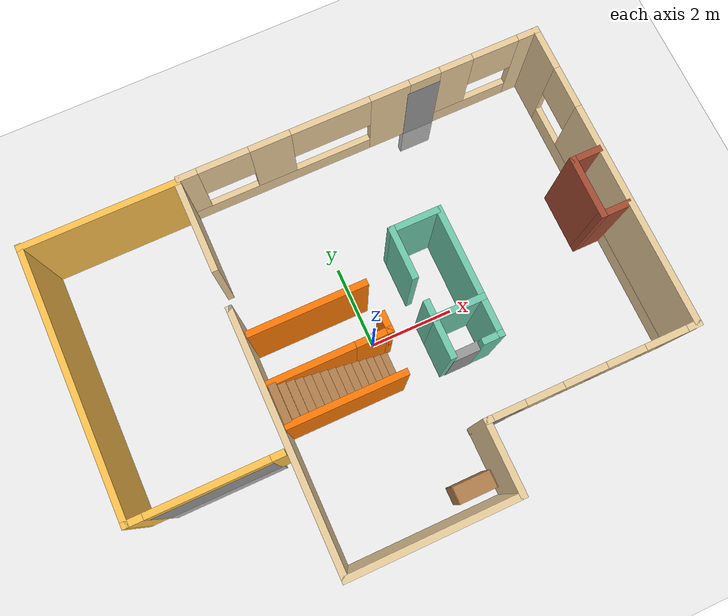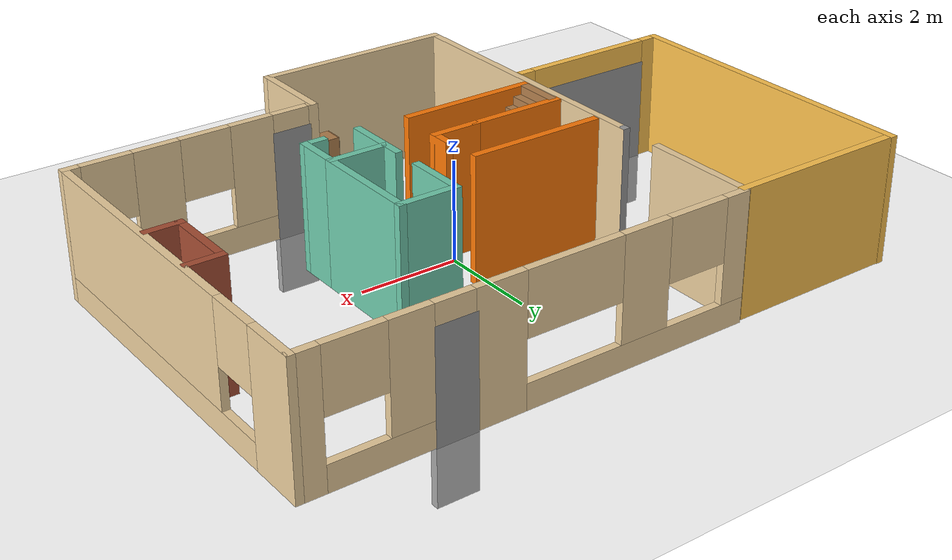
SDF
<sdf version="1.6">
 <world name="default">
  <light name="sun" type="directional">
   <pose>0 0 10 0 -0 0</pose>
   <diffuse>0.8 0.8 0.8 1</diffuse>
   <specular>0.2 0.2 0.2 1</specular>
   <attenuation>
    <range>1000</range>
    <constant>0.9</constant>
    <linear>0.01</linear>
    <quadratic>0.001</quadratic>
   </attenuation>
   <direction>-0.5 0.1 -0.9</direction>
  </light>
  <model name="ground_plane">
   <static>1</static>
   <link name="link">
    <collision name="collision">
     <geometry><plane><normal>0 0 1</normal><size>100 100</size></plane></geometry>
     <surface><friction><ode><mu>100</mu><mu2>50</mu2></ode></friction></surface>
    </collision>
    <visual name="visual">
     <cast_shadows>0</cast_shadows>
     <geometry><plane><normal>0 0 1</normal><size>100 100</size></plane></geometry>
     <material>
      <script><uri>file://media/materials/scripts/gazebo.material</uri><name>Gazebo/Grey</name></script>
     </material>
    </visual>
   </link>
  </model>
  <gravity>0 0 -9.8</gravity>
  <magnetic_field>6e-06 2.3e-05 -4.2e-05</magnetic_field>
  <atmosphere type="adiabatic"/>
  <physics name="default_physics" default="0" type="ode">
   <max_step_size>0.001</max_step_size>
   <real_time_factor>1</real_time_factor>
   <real_time_update_rate>1000</real_time_update_rate>
  </physics>
  <scene><ambient>0.4 0.4 0.4 1</ambient><background>0.7 0.7 0.7 1</background><shadows>1</shadows></scene>
  <spherical_coordinates>
   <surface_model>EARTH_WGS84</surface_model>
   <latitude_deg>0</latitude_deg>
   <longitude_deg>0</longitude_deg>
   <elevation>0</elevation>
   <heading_deg>0</heading_deg>
  </spherical_coordinates>
  <model name="my_world">
   <link name="Door_2">
    <pose>0.765403 -1.37888 0 0 -0 0</pose>
    <visual name="Door_2_Visual">
     <pose>0 0 1 0 -0 0</pose>
     <geometry><box><size>0.626242 0.2 2</size></box></geometry>
     <material>
      <script><uri>file://media/materials/scripts/gazebo.material</uri><name>Gazebo/Grey</name></script>
      <ambient>0.3 0.3 0.3 1</ambient>
      <diffuse>0.7 0.7 0.7 1</diffuse>
      <specular>0.01 0.01 0.01 1</specular>
      <emissive>0 0 0 1</emissive>
      <shader type="pixel"/>
     </material>
    </visual>
    <collision name="Door_2_Collision">
     <pose>0 0 1 0 -0 0</pose>
     <geometry><box><size>0.626242 0.2 2</size></box></geometry>
     <surface>
      <friction>
       <ode><mu>1</mu><mu2>1</mu2><fdir1>0 0 0</fdir1><slip1>0</slip1><slip2>0</slip2></ode>
       <torsional>
        <coefficient>1</coefficient>
        <patch_radius>0</patch_radius>
        <surface_radius>0</surface_radius>
        <use_patch_radius>1</use_patch_radius>
        <ode><slip>0</slip></ode>
       </torsional>
      </friction>
      <bounce><restitution_coefficient>0</restitution_coefficient><threshold>1e+06</threshold></bounce>
      <contact>
       <collide_without_contact>0</collide_without_contact>
       <collide_without_contact_bitmask>1</collide_without_contact_bitmask>
       <collide_bitmask>1</collide_bitmask>
       <ode>
        <soft_cfm>0</soft_cfm>
        <soft_erp>0.2</soft_erp>
        <kp>1e+13</kp>
        <kd>1</kd>
        <max_vel>0.01</max_vel>
        <min_depth>0</min_depth>
       </ode>
       <bullet>
        <split_impulse>1</split_impulse>
        <split_impulse_penetration_threshold>-0.01</split_impulse_penetration_threshold>
        <soft_cfm>0</soft_cfm>
        <soft_erp>0.2</soft_erp>
        <kp>1e+13</kp>
        <kd>1</kd>
       </bullet>
      </contact>
     </surface>
    </collision>
   </link>
   <link name="Stairs_3">
    <visual name="Stairs_3_Visual_0">
     <pose>-0.655687 -0.838968 0.083333 0 0 -1.5708</pose>
     <geometry><box><size>0.863121 0.182638 0.166667</size></box></geometry>
     <material>
      <script><uri>file://media/materials/scripts/gazebo.material</uri><name>Gazebo/Wood</name></script>
      <ambient>1 1 1 1</ambient>
      <diffuse>1 1 1 1</diffuse>
      <specular>0.2 0.2 0.2 1</specular>
      <emissive>0 0 0 1</emissive>
      <shader type="pixel"/>
     </material>
     <meta><layer>0</layer></meta>
    </visual>
    <visual name="Stairs_3_Visual_1">
     <pose>-0.838325 -0.838968 0.25 0 0 -1.5708</pose>
     <geometry><box><size>0.863121 0.182638 0.166667</size></box></geometry>
     <material>
      <script><uri>file://media/materials/scripts/gazebo.material</uri><name>Gazebo/Wood</name></script>
      <ambient>1 1 1 1</ambient>
      <diffuse>1 1 1 1</diffuse>
      <specular>0.2 0.2 0.2 1</specular>
      <emissive>0 0 0 1</emissive>
      <shader type="pixel"/>
     </material>
     <meta><layer>0</layer></meta>
    </visual>
    <visual name="Stairs_3_Visual_2">
     <pose>-1.02096 -0.838968 0.416667 0 0 -1.5708</pose>
     <geometry><box><size>0.863121 0.182638 0.166667</size></box></geometry>
     <material>
      <script><uri>file://media/materials/scripts/gazebo.material</uri><name>Gazebo/Wood</name></script>
      <ambient>1 1 1 1</ambient>
      <diffuse>1 1 1 1</diffuse>
      <specular>0.2 0.2 0.2 1</specular>
      <emissive>0 0 0 1</emissive>
      <shader type="pixel"/>
     </material>
     <meta><layer>0</layer></meta>
    </visual>
    <visual name="Stairs_3_Visual_8">
     <pose>-2.11679 -0.838967 1.41667 0 0 -1.5708</pose>
     <geometry><box><size>0.863121 0.182638 0.166667</size></box></geometry>
     <material>
      <script><uri>file://media/materials/scripts/gazebo.material</uri><name>Gazebo/Wood</name></script>
      <ambient>1 1 1 1</ambient>
      <diffuse>1 1 1 1</diffuse>
      <specular>0.2 0.2 0.2 1</specular>
      <emissive>0 0 0 1</emissive>
      <shader type="pixel"/>
     </material>
     <meta><layer>0</layer></meta>
    </visual>
    <visual name="Stairs_3_Visual_3">
     <pose>-1.2036 -0.838968 0.583333 0 0 -1.5708</pose>
     <geometry><box><size>0.863121 0.182638 0.166667</size></box></geometry>
     <material>
      <script><uri>file://media/materials/scripts/gazebo.material</uri><name>Gazebo/Wood</name></script>
      <ambient>1 1 1 1</ambient>
      <diffuse>1 1 1 1</diffuse>
      <specular>0.2 0.2 0.2 1</specular>
      <emissive>0 0 0 1</emissive>
      <shader type="pixel"/>
     </material>
     <meta><layer>0</layer></meta>
    </visual>
    <visual name="Stairs_3_Visual_4">
     <pose>-1.38624 -0.838968 0.75 0 0 -1.5708</pose>
     <geometry><box><size>0.863121 0.182638 0.166667</size></box></geometry>
     <material>
      <script><uri>file://media/materials/scripts/gazebo.material</uri><name>Gazebo/Wood</name></script>
      <ambient>1 1 1 1</ambient>
      <diffuse>1 1 1 1</diffuse>
      <specular>0.2 0.2 0.2 1</specular>
      <emissive>0 0 0 1</emissive>
      <shader type="pixel"/>
     </material>
     <meta><layer>0</layer></meta>
    </visual>
    <visual name="Stairs_3_Visual_5">
     <pose>-1.56888 -0.838968 0.916667 0 0 -1.5708</pose>
     <geometry><box><size>0.863121 0.182638 0.166667</size></box></geometry>
     <material>
      <script><uri>file://media/materials/scripts/gazebo.material</uri><name>Gazebo/Wood</name></script>
      <ambient>1 1 1 1</ambient>
      <diffuse>1 1 1 1</diffuse>
      <specular>0.2 0.2 0.2 1</specular>
      <emissive>0 0 0 1</emissive>
      <shader type="pixel"/>
     </material>
     <meta><layer>0</layer></meta>
    </visual>
    <visual name="Stairs_3_Visual_6">
     <pose>-1.75151 -0.838968 1.08333 0 0 -1.5708</pose>
     <geometry><box><size>0.863121 0.182638 0.166667</size></box></geometry>
     <material>
      <script><uri>file://media/materials/scripts/gazebo.material</uri><name>Gazebo/Wood</name></script>
      <ambient>1 1 1 1</ambient>
      <diffuse>1 1 1 1</diffuse>
      <specular>0.2 0.2 0.2 1</specular>
      <emissive>0 0 0 1</emissive>
      <shader type="pixel"/>
     </material>
     <meta><layer>0</layer></meta>
    </visual>
    <visual name="Stairs_3_Visual_7">
     <pose>-1.93415 -0.838968 1.25 0 0 -1.5708</pose>
     <geometry><box><size>0.863121 0.182638 0.166667</size></box></geometry>
     <material>
      <script><uri>file://media/materials/scripts/gazebo.material</uri><name>Gazebo/Wood</name></script>
      <ambient>1 1 1 1</ambient>
      <diffuse>1 1 1 1</diffuse>
      <specular>0.2 0.2 0.2 1</specular>
      <emissive>0 0 0 1</emissive>
      <shader type="pixel"/>
     </material>
     <meta><layer>0</layer></meta>
    </visual>
    <visual name="Stairs_3_Visual_9">
     <pose>-2.29942 -0.838967 1.58333 0 0 -1.5708</pose>
     <geometry><box><size>0.863121 0.182638 0.166667</size></box></geometry>
     <material>
      <script><uri>file://media/materials/scripts/gazebo.material</uri><name>Gazebo/Wood</name></script>
      <ambient>1 1 1 1</ambient>
      <diffuse>1 1 1 1</diffuse>
      <specular>0.2 0.2 0.2 1</specular>
      <emissive>0 0 0 1</emissive>
      <shader type="pixel"/>
     </material>
     <meta><layer>0</layer></meta>
    </visual>
    <visual name="Stairs_3_Visual_10">
     <pose>-2.48206 -0.838967 1.75 0 0 -1.5708</pose>
     <geometry><box><size>0.863121 0.182638 0.166667</size></box></geometry>
     <material>
      <script><uri>file://media/materials/scripts/gazebo.material</uri><name>Gazebo/Wood</name></script>
      <ambient>1 1 1 1</ambient>
      <diffuse>1 1 1 1</diffuse>
      <specular>0.2 0.2 0.2 1</specular>
      <emissive>0 0 0 1</emissive>
      <shader type="pixel"/>
     </material>
     <meta><layer>0</layer></meta>
    </visual>
    <visual name="Stairs_3_Visual_11">
     <pose>-2.6647 -0.838967 1.91667 0 0 -1.5708</pose>
     <geometry><box><size>0.863121 0.182638 0.166667</size></box></geometry>
     <material>
      <script><uri>file://media/materials/scripts/gazebo.material</uri><name>Gazebo/Wood</name></script>
      <ambient>1 1 1 1</ambient>
      <diffuse>1 1 1 1</diffuse>
      <specular>0.2 0.2 0.2 1</specular>
      <emissive>0 0 0 1</emissive>
      <shader type="pixel"/>
     </material>
     <meta><layer>0</layer></meta>
    </visual>
    <visual name="Stairs_3_Visual_12">
     <pose>-2.84734 -0.838967 2.08333 0 0 -1.5708</pose>
     <geometry><box><size>0.863121 0.182638 0.166667</size></box></geometry>
     <material>
      <script><uri>file://media/materials/scripts/gazebo.material</uri><name>Gazebo/Wood</name></script>
      <ambient>1 1 1 1</ambient>
      <diffuse>1 1 1 1</diffuse>
      <specular>0.2 0.2 0.2 1</specular>
      <emissive>0 0 0 1</emissive>
      <shader type="pixel"/>
     </material>
     <meta><layer>0</layer></meta>
    </visual>
    <visual name="Stairs_3_Visual_13">
     <pose>-3.02997 -0.838967 2.25 0 0 -1.5708</pose>
     <geometry><box><size>0.863121 0.182638 0.166667</size></box></geometry>
     <material>
      <script><uri>file://media/materials/scripts/gazebo.material</uri><name>Gazebo/Wood</name></script>
      <ambient>1 1 1 1</ambient>
      <diffuse>1 1 1 1</diffuse>
      <specular>0.2 0.2 0.2 1</specular>
      <emissive>0 0 0 1</emissive>
      <shader type="pixel"/>
     </material>
     <meta><layer>0</layer></meta>
    </visual>
    <visual name="Stairs_3_Visual_14">
     <pose>-3.21261 -0.838967 2.41667 0 0 -1.5708</pose>
     <geometry><box><size>0.863121 0.182638 0.166667</size></box></geometry>
     <material>
      <script><uri>file://media/materials/scripts/gazebo.material</uri><name>Gazebo/Wood</name></script>
      <ambient>1 1 1 1</ambient>
      <diffuse>1 1 1 1</diffuse>
      <specular>0.2 0.2 0.2 1</specular>
      <emissive>0 0 0 1</emissive>
      <shader type="pixel"/>
     </material>
     <meta><layer>0</layer></meta>
    </visual>
    <collision name="Stairs_3_Collision_13">
     <pose>-3.02997 -0.838967 2.25 0 0 -1.5708</pose>
     <geometry><box><size>0.863121 0.182638 0.166667</size></box></geometry>
     <surface>
      <friction>
       <ode><mu>1</mu><mu2>1</mu2><fdir1>0 0 0</fdir1><slip1>0</slip1><slip2>0</slip2></ode>
       <torsional>
        <coefficient>1</coefficient>
        <patch_radius>0</patch_radius>
        <surface_radius>0</surface_radius>
        <use_patch_radius>1</use_patch_radius>
        <ode><slip>0</slip></ode>
       </torsional>
      </friction>
      <bounce><restitution_coefficient>0</restitution_coefficient><threshold>1e+06</threshold></bounce>
      <contact>
       <collide_without_contact>0</collide_without_contact>
       <collide_without_contact_bitmask>1</collide_without_contact_bitmask>
       <collide_bitmask>1</collide_bitmask>
       <ode>
        <soft_cfm>0</soft_cfm>
        <soft_erp>0.2</soft_erp>
        <kp>1e+13</kp>
        <kd>1</kd>
        <max_vel>0.01</max_vel>
        <min_depth>0</min_depth>
       </ode>
       <bullet>
        <split_impulse>1</split_impulse>
        <split_impulse_penetration_threshold>-0.01</split_impulse_penetration_threshold>
        <soft_cfm>0</soft_cfm>
        <soft_erp>0.2</soft_erp>
        <kp>1e+13</kp>
        <kd>1</kd>
       </bullet>
      </contact>
     </surface>
    </collision>
    <collision name="Stairs_3_Collision_2">
     <pose>-1.02096 -0.838968 0.416667 0 0 -1.5708</pose>
     <geometry><box><size>0.863121 0.182638 0.166667</size></box></geometry>
     <surface>
      <friction>
       <ode><mu>1</mu><mu2>1</mu2><fdir1>0 0 0</fdir1><slip1>0</slip1><slip2>0</slip2></ode>
       <torsional>
        <coefficient>1</coefficient>
        <patch_radius>0</patch_radius>
        <surface_radius>0</surface_radius>
        <use_patch_radius>1</use_patch_radius>
        <ode><slip>0</slip></ode>
       </torsional>
      </friction>
      <bounce><restitution_coefficient>0</restitution_coefficient><threshold>1e+06</threshold></bounce>
      <contact>
       <collide_without_contact>0</collide_without_contact>
       <collide_without_contact_bitmask>1</collide_without_contact_bitmask>
       <collide_bitmask>1</collide_bitmask>
       <ode>
        <soft_cfm>0</soft_cfm>
        <soft_erp>0.2</soft_erp>
        <kp>1e+13</kp>
        <kd>1</kd>
        <max_vel>0.01</max_vel>
        <min_depth>0</min_depth>
       </ode>
       <bullet>
        <split_impulse>1</split_impulse>
        <split_impulse_penetration_threshold>-0.01</split_impulse_penetration_threshold>
        <soft_cfm>0</soft_cfm>
        <soft_erp>0.2</soft_erp>
        <kp>1e+13</kp>
        <kd>1</kd>
       </bullet>
      </contact>
     </surface>
    </collision>
    <collision name="Stairs_3_Collision_0">
     <pose>-0.655687 -0.838968 0.083333 0 0 -1.5708</pose>
     <geometry><box><size>0.863121 0.182638 0.166667</size></box></geometry>
     <surface>
      <friction>
       <ode><mu>1</mu><mu2>1</mu2><fdir1>0 0 0</fdir1><slip1>0</slip1><slip2>0</slip2></ode>
       <torsional>
        <coefficient>1</coefficient>
        <patch_radius>0</patch_radius>
        <surface_radius>0</surface_radius>
        <use_patch_radius>1</use_patch_radius>
        <ode><slip>0</slip></ode>
       </torsional>
      </friction>
      <bounce><restitution_coefficient>0</restitution_coefficient><threshold>1e+06</threshold></bounce>
      <contact>
       <collide_without_contact>0</collide_without_contact>
       <collide_without_contact_bitmask>1</collide_without_contact_bitmask>
       <collide_bitmask>1</collide_bitmask>
       <ode>
        <soft_cfm>0</soft_cfm>
        <soft_erp>0.2</soft_erp>
        <kp>1e+13</kp>
        <kd>1</kd>
        <max_vel>0.01</max_vel>
        <min_depth>0</min_depth>
       </ode>
       <bullet>
        <split_impulse>1</split_impulse>
        <split_impulse_penetration_threshold>-0.01</split_impulse_penetration_threshold>
        <soft_cfm>0</soft_cfm>
        <soft_erp>0.2</soft_erp>
        <kp>1e+13</kp>
        <kd>1</kd>
       </bullet>
      </contact>
     </surface>
    </collision>
    <collision name="Stairs_3_Collision_1">
     <pose>-0.838325 -0.838968 0.25 0 0 -1.5708</pose>
     <geometry><box><size>0.863121 0.182638 0.166667</size></box></geometry>
     <surface>
      <friction>
       <ode><mu>1</mu><mu2>1</mu2><fdir1>0 0 0</fdir1><slip1>0</slip1><slip2>0</slip2></ode>
       <torsional>
        <coefficient>1</coefficient>
        <patch_radius>0</patch_radius>
        <surface_radius>0</surface_radius>
        <use_patch_radius>1</use_patch_radius>
        <ode><slip>0</slip></ode>
       </torsional>
      </friction>
      <bounce><restitution_coefficient>0</restitution_coefficient><threshold>1e+06</threshold></bounce>
      <contact>
       <collide_without_contact>0</collide_without_contact>
       <collide_without_contact_bitmask>1</collide_without_contact_bitmask>
       <collide_bitmask>1</collide_bitmask>
       <ode>
        <soft_cfm>0</soft_cfm>
        <soft_erp>0.2</soft_erp>
        <kp>1e+13</kp>
        <kd>1</kd>
        <max_vel>0.01</max_vel>
        <min_depth>0</min_depth>
       </ode>
       <bullet>
        <split_impulse>1</split_impulse>
        <split_impulse_penetration_threshold>-0.01</split_impulse_penetration_threshold>
        <soft_cfm>0</soft_cfm>
        <soft_erp>0.2</soft_erp>
        <kp>1e+13</kp>
        <kd>1</kd>
       </bullet>
      </contact>
     </surface>
    </collision>
    <collision name="Stairs_3_Collision_3">
     <pose>-1.2036 -0.838968 0.583333 0 0 -1.5708</pose>
     <geometry><box><size>0.863121 0.182638 0.166667</size></box></geometry>
     <surface>
      <friction>
       <ode><mu>1</mu><mu2>1</mu2><fdir1>0 0 0</fdir1><slip1>0</slip1><slip2>0</slip2></ode>
       <torsional>
        <coefficient>1</coefficient>
        <patch_radius>0</patch_radius>
        <surface_radius>0</surface_radius>
        <use_patch_radius>1</use_patch_radius>
        <ode><slip>0</slip></ode>
       </torsional>
      </friction>
      <bounce><restitution_coefficient>0</restitution_coefficient><threshold>1e+06</threshold></bounce>
      <contact>
       <collide_without_contact>0</collide_without_contact>
       <collide_without_contact_bitmask>1</collide_without_contact_bitmask>
       <collide_bitmask>1</collide_bitmask>
       <ode>
        <soft_cfm>0</soft_cfm>
        <soft_erp>0.2</soft_erp>
        <kp>1e+13</kp>
        <kd>1</kd>
        <max_vel>0.01</max_vel>
        <min_depth>0</min_depth>
       </ode>
       <bullet>
        <split_impulse>1</split_impulse>
        <split_impulse_penetration_threshold>-0.01</split_impulse_penetration_threshold>
        <soft_cfm>0</soft_cfm>
        <soft_erp>0.2</soft_erp>
        <kp>1e+13</kp>
        <kd>1</kd>
       </bullet>
      </contact>
     </surface>
    </collision>
    <collision name="Stairs_3_Collision_4">
     <pose>-1.38624 -0.838968 0.75 0 0 -1.5708</pose>
     <geometry><box><size>0.863121 0.182638 0.166667</size></box></geometry>
     <surface>
      <friction>
       <ode><mu>1</mu><mu2>1</mu2><fdir1>0 0 0</fdir1><slip1>0</slip1><slip2>0</slip2></ode>
       <torsional>
        <coefficient>1</coefficient>
        <patch_radius>0</patch_radius>
        <surface_radius>0</surface_radius>
        <use_patch_radius>1</use_patch_radius>
        <ode><slip>0</slip></ode>
       </torsional>
      </friction>
      <bounce><restitution_coefficient>0</restitution_coefficient><threshold>1e+06</threshold></bounce>
      <contact>
       <collide_without_contact>0</collide_without_contact>
       <collide_without_contact_bitmask>1</collide_without_contact_bitmask>
       <collide_bitmask>1</collide_bitmask>
       <ode>
        <soft_cfm>0</soft_cfm>
        <soft_erp>0.2</soft_erp>
        <kp>1e+13</kp>
        <kd>1</kd>
        <max_vel>0.01</max_vel>
        <min_depth>0</min_depth>
       </ode>
       <bullet>
        <split_impulse>1</split_impulse>
        <split_impulse_penetration_threshold>-0.01</split_impulse_penetration_threshold>
        <soft_cfm>0</soft_cfm>
        <soft_erp>0.2</soft_erp>
        <kp>1e+13</kp>
        <kd>1</kd>
       </bullet>
      </contact>
     </surface>
    </collision>
    <collision name="Stairs_3_Collision_5">
     <pose>-1.56888 -0.838968 0.916667 0 0 -1.5708</pose>
     <geometry><box><size>0.863121 0.182638 0.166667</size></box></geometry>
     <surface>
      <friction>
       <ode><mu>1</mu><mu2>1</mu2><fdir1>0 0 0</fdir1><slip1>0</slip1><slip2>0</slip2></ode>
       <torsional>
        <coefficient>1</coefficient>
        <patch_radius>0</patch_radius>
        <surface_radius>0</surface_radius>
        <use_patch_radius>1</use_patch_radius>
        <ode><slip>0</slip></ode>
       </torsional>
      </friction>
      <bounce><restitution_coefficient>0</restitution_coefficient><threshold>1e+06</threshold></bounce>
      <contact>
       <collide_without_contact>0</collide_without_contact>
       <collide_without_contact_bitmask>1</collide_without_contact_bitmask>
       <collide_bitmask>1</collide_bitmask>
       <ode>
        <soft_cfm>0</soft_cfm>
        <soft_erp>0.2</soft_erp>
        <kp>1e+13</kp>
        <kd>1</kd>
        <max_vel>0.01</max_vel>
        <min_depth>0</min_depth>
       </ode>
       <bullet>
        <split_impulse>1</split_impulse>
        <split_impulse_penetration_threshold>-0.01</split_impulse_penetration_threshold>
        <soft_cfm>0</soft_cfm>
        <soft_erp>0.2</soft_erp>
        <kp>1e+13</kp>
        <kd>1</kd>
       </bullet>
      </contact>
     </surface>
    </collision>
    <collision name="Stairs_3_Collision_7">
     <pose>-1.93415 -0.838968 1.25 0 0 -1.5708</pose>
     <geometry><box><size>0.863121 0.182638 0.166667</size></box></geometry>
     <surface>
      <friction>
       <ode><mu>1</mu><mu2>1</mu2><fdir1>0 0 0</fdir1><slip1>0</slip1><slip2>0</slip2></ode>
       <torsional>
        <coefficient>1</coefficient>
        <patch_radius>0</patch_radius>
        <surface_radius>0</surface_radius>
        <use_patch_radius>1</use_patch_radius>
        <ode><slip>0</slip></ode>
       </torsional>
      </friction>
      <bounce><restitution_coefficient>0</restitution_coefficient><threshold>1e+06</threshold></bounce>
      <contact>
       <collide_without_contact>0</collide_without_contact>
       <collide_without_contact_bitmask>1</collide_without_contact_bitmask>
       <collide_bitmask>1</collide_bitmask>
       <ode>
        <soft_cfm>0</soft_cfm>
        <soft_erp>0.2</soft_erp>
        <kp>1e+13</kp>
        <kd>1</kd>
        <max_vel>0.01</max_vel>
        <min_depth>0</min_depth>
       </ode>
       <bullet>
        <split_impulse>1</split_impulse>
        <split_impulse_penetration_threshold>-0.01</split_impulse_penetration_threshold>
        <soft_cfm>0</soft_cfm>
        <soft_erp>0.2</soft_erp>
        <kp>1e+13</kp>
        <kd>1</kd>
       </bullet>
      </contact>
     </surface>
    </collision>
    <collision name="Stairs_3_Collision_6">
     <pose>-1.75151 -0.838968 1.08333 0 0 -1.5708</pose>
     <geometry><box><size>0.863121 0.182638 0.166667</size></box></geometry>
     <surface>
      <friction>
       <ode><mu>1</mu><mu2>1</mu2><fdir1>0 0 0</fdir1><slip1>0</slip1><slip2>0</slip2></ode>
       <torsional>
        <coefficient>1</coefficient>
        <patch_radius>0</patch_radius>
        <surface_radius>0</surface_radius>
        <use_patch_radius>1</use_patch_radius>
        <ode><slip>0</slip></ode>
       </torsional>
      </friction>
      <bounce><restitution_coefficient>0</restitution_coefficient><threshold>1e+06</threshold></bounce>
      <contact>
       <collide_without_contact>0</collide_without_contact>
       <collide_without_contact_bitmask>1</collide_without_contact_bitmask>
       <collide_bitmask>1</collide_bitmask>
       <ode>
        <soft_cfm>0</soft_cfm>
        <soft_erp>0.2</soft_erp>
        <kp>1e+13</kp>
        <kd>1</kd>
        <max_vel>0.01</max_vel>
        <min_depth>0</min_depth>
       </ode>
       <bullet>
        <split_impulse>1</split_impulse>
        <split_impulse_penetration_threshold>-0.01</split_impulse_penetration_threshold>
        <soft_cfm>0</soft_cfm>
        <soft_erp>0.2</soft_erp>
        <kp>1e+13</kp>
        <kd>1</kd>
       </bullet>
      </contact>
     </surface>
    </collision>
    <collision name="Stairs_3_Collision_8">
     <pose>-2.11679 -0.838967 1.41667 0 0 -1.5708</pose>
     <geometry><box><size>0.863121 0.182638 0.166667</size></box></geometry>
     <surface>
      <friction>
       <ode><mu>1</mu><mu2>1</mu2><fdir1>0 0 0</fdir1><slip1>0</slip1><slip2>0</slip2></ode>
       <torsional>
        <coefficient>1</coefficient>
        <patch_radius>0</patch_radius>
        <surface_radius>0</surface_radius>
        <use_patch_radius>1</use_patch_radius>
        <ode><slip>0</slip></ode>
       </torsional>
      </friction>
      <bounce><restitution_coefficient>0</restitution_coefficient><threshold>1e+06</threshold></bounce>
      <contact>
       <collide_without_contact>0</collide_without_contact>
       <collide_without_contact_bitmask>1</collide_without_contact_bitmask>
       <collide_bitmask>1</collide_bitmask>
       <ode>
        <soft_cfm>0</soft_cfm>
        <soft_erp>0.2</soft_erp>
        <kp>1e+13</kp>
        <kd>1</kd>
        <max_vel>0.01</max_vel>
        <min_depth>0</min_depth>
       </ode>
       <bullet>
        <split_impulse>1</split_impulse>
        <split_impulse_penetration_threshold>-0.01</split_impulse_penetration_threshold>
        <soft_cfm>0</soft_cfm>
        <soft_erp>0.2</soft_erp>
        <kp>1e+13</kp>
        <kd>1</kd>
       </bullet>
      </contact>
     </surface>
    </collision>
    <collision name="Stairs_3_Collision_9">
     <pose>-2.29942 -0.838967 1.58333 0 0 -1.5708</pose>
     <geometry><box><size>0.863121 0.182638 0.166667</size></box></geometry>
     <surface>
      <friction>
       <ode><mu>1</mu><mu2>1</mu2><fdir1>0 0 0</fdir1><slip1>0</slip1><slip2>0</slip2></ode>
       <torsional>
        <coefficient>1</coefficient>
        <patch_radius>0</patch_radius>
        <surface_radius>0</surface_radius>
        <use_patch_radius>1</use_patch_radius>
        <ode><slip>0</slip></ode>
       </torsional>
      </friction>
      <bounce><restitution_coefficient>0</restitution_coefficient><threshold>1e+06</threshold></bounce>
      <contact>
       <collide_without_contact>0</collide_without_contact>
       <collide_without_contact_bitmask>1</collide_without_contact_bitmask>
       <collide_bitmask>1</collide_bitmask>
       <ode>
        <soft_cfm>0</soft_cfm>
        <soft_erp>0.2</soft_erp>
        <kp>1e+13</kp>
        <kd>1</kd>
        <max_vel>0.01</max_vel>
        <min_depth>0</min_depth>
       </ode>
       <bullet>
        <split_impulse>1</split_impulse>
        <split_impulse_penetration_threshold>-0.01</split_impulse_penetration_threshold>
        <soft_cfm>0</soft_cfm>
        <soft_erp>0.2</soft_erp>
        <kp>1e+13</kp>
        <kd>1</kd>
       </bullet>
      </contact>
     </surface>
    </collision>
    <collision name="Stairs_3_Collision_11">
     <pose>-2.6647 -0.838967 1.91667 0 0 -1.5708</pose>
     <geometry><box><size>0.863121 0.182638 0.166667</size></box></geometry>
     <surface>
      <friction>
       <ode><mu>1</mu><mu2>1</mu2><fdir1>0 0 0</fdir1><slip1>0</slip1><slip2>0</slip2></ode>
       <torsional>
        <coefficient>1</coefficient>
        <patch_radius>0</patch_radius>
        <surface_radius>0</surface_radius>
        <use_patch_radius>1</use_patch_radius>
        <ode><slip>0</slip></ode>
       </torsional>
      </friction>
      <bounce><restitution_coefficient>0</restitution_coefficient><threshold>1e+06</threshold></bounce>
      <contact>
       <collide_without_contact>0</collide_without_contact>
       <collide_without_contact_bitmask>1</collide_without_contact_bitmask>
       <collide_bitmask>1</collide_bitmask>
       <ode>
        <soft_cfm>0</soft_cfm>
        <soft_erp>0.2</soft_erp>
        <kp>1e+13</kp>
        <kd>1</kd>
        <max_vel>0.01</max_vel>
        <min_depth>0</min_depth>
       </ode>
       <bullet>
        <split_impulse>1</split_impulse>
        <split_impulse_penetration_threshold>-0.01</split_impulse_penetration_threshold>
        <soft_cfm>0</soft_cfm>
        <soft_erp>0.2</soft_erp>
        <kp>1e+13</kp>
        <kd>1</kd>
       </bullet>
      </contact>
     </surface>
    </collision>
    <collision name="Stairs_3_Collision_12">
     <pose>-2.84734 -0.838967 2.08333 0 0 -1.5708</pose>
     <geometry><box><size>0.863121 0.182638 0.166667</size></box></geometry>
     <surface>
      <friction>
       <ode><mu>1</mu><mu2>1</mu2><fdir1>0 0 0</fdir1><slip1>0</slip1><slip2>0</slip2></ode>
       <torsional>
        <coefficient>1</coefficient>
        <patch_radius>0</patch_radius>
        <surface_radius>0</surface_radius>
        <use_patch_radius>1</use_patch_radius>
        <ode><slip>0</slip></ode>
       </torsional>
      </friction>
      <bounce><restitution_coefficient>0</restitution_coefficient><threshold>1e+06</threshold></bounce>
      <contact>
       <collide_without_contact>0</collide_without_contact>
       <collide_without_contact_bitmask>1</collide_without_contact_bitmask>
       <collide_bitmask>1</collide_bitmask>
       <ode>
        <soft_cfm>0</soft_cfm>
        <soft_erp>0.2</soft_erp>
        <kp>1e+13</kp>
        <kd>1</kd>
        <max_vel>0.01</max_vel>
        <min_depth>0</min_depth>
       </ode>
       <bullet>
        <split_impulse>1</split_impulse>
        <split_impulse_penetration_threshold>-0.01</split_impulse_penetration_threshold>
        <soft_cfm>0</soft_cfm>
        <soft_erp>0.2</soft_erp>
        <kp>1e+13</kp>
        <kd>1</kd>
       </bullet>
      </contact>
     </surface>
    </collision>
    <collision name="Stairs_3_Collision_10">
     <pose>-2.48206 -0.838967 1.75 0 0 -1.5708</pose>
     <geometry><box><size>0.863121 0.182638 0.166667</size></box></geometry>
     <surface>
      <friction>
       <ode><mu>1</mu><mu2>1</mu2><fdir1>0 0 0</fdir1><slip1>0</slip1><slip2>0</slip2></ode>
       <torsional>
        <coefficient>1</coefficient>
        <patch_radius>0</patch_radius>
        <surface_radius>0</surface_radius>
        <use_patch_radius>1</use_patch_radius>
        <ode><slip>0</slip></ode>
       </torsional>
      </friction>
      <bounce><restitution_coefficient>0</restitution_coefficient><threshold>1e+06</threshold></bounce>
      <contact>
       <collide_without_contact>0</collide_without_contact>
       <collide_without_contact_bitmask>1</collide_without_contact_bitmask>
       <collide_bitmask>1</collide_bitmask>
       <ode>
        <soft_cfm>0</soft_cfm>
        <soft_erp>0.2</soft_erp>
        <kp>1e+13</kp>
        <kd>1</kd>
        <max_vel>0.01</max_vel>
        <min_depth>0</min_depth>
       </ode>
       <bullet>
        <split_impulse>1</split_impulse>
        <split_impulse_penetration_threshold>-0.01</split_impulse_penetration_threshold>
        <soft_cfm>0</soft_cfm>
        <soft_erp>0.2</soft_erp>
        <kp>1e+13</kp>
        <kd>1</kd>
       </bullet>
      </contact>
     </surface>
    </collision>
    <collision name="Stairs_3_Collision_14">
     <pose>-3.21261 -0.838967 2.41667 0 0 -1.5708</pose>
     <geometry><box><size>0.863121 0.182638 0.166667</size></box></geometry>
     <surface>
      <friction>
       <ode><mu>1</mu><mu2>1</mu2><fdir1>0 0 0</fdir1><slip1>0</slip1><slip2>0</slip2></ode>
       <torsional>
        <coefficient>1</coefficient>
        <patch_radius>0</patch_radius>
        <surface_radius>0</surface_radius>
        <use_patch_radius>1</use_patch_radius>
        <ode><slip>0</slip></ode>
       </torsional>
      </friction>
      <bounce><restitution_coefficient>0</restitution_coefficient><threshold>1e+06</threshold></bounce>
      <contact>
       <collide_without_contact>0</collide_without_contact>
       <collide_without_contact_bitmask>1</collide_without_contact_bitmask>
       <collide_bitmask>1</collide_bitmask>
       <ode>
        <soft_cfm>0</soft_cfm>
        <soft_erp>0.2</soft_erp>
        <kp>1e+13</kp>
        <kd>1</kd>
        <max_vel>0.01</max_vel>
        <min_depth>0</min_depth>
       </ode>
       <bullet>
        <split_impulse>1</split_impulse>
        <split_impulse_penetration_threshold>-0.01</split_impulse_penetration_threshold>
        <soft_cfm>0</soft_cfm>
        <soft_erp>0.2</soft_erp>
        <kp>1e+13</kp>
        <kd>1</kd>
       </bullet>
      </contact>
     </surface>
    </collision>
   </link>
   <link name="Wall_0">
    <pose>5.30002 0.8 0 0 0 -1.5708</pose>
    <visual name="Wall_0_Visual_0">
     <pose>-3.20604 0 1.25 0 -0 0</pose>
     <geometry><box><size>1.08792 0.15 2.5</size></box></geometry>
     <material>
      <script><uri>file://media/materials/scripts/gazebo.material</uri><name>Gazebo/Grey</name></script>
      <ambient>0.921569 0.807843 0.615686 1</ambient>
      <diffuse>0.7 0.7 0.7 1</diffuse>
      <specular>0.01 0.01 0.01 1</specular>
      <emissive>0 0 0 1</emissive>
      <shader type="pixel"/>
     </material>
     <meta><layer>0</layer></meta>
    </visual>
    <visual name="Wall_0_Visual_1">
     <pose>0.543962 0 0.25 0 -0 0</pose>
     <geometry><box><size>6.41208 0.15 0.5</size></box></geometry>
     <material>
      <script><uri>file://media/materials/scripts/gazebo.material</uri><name>Gazebo/Grey</name></script>
      <ambient>0.921569 0.807843 0.615686 1</ambient>
      <diffuse>0.7 0.7 0.7 1</diffuse>
      <specular>0.01 0.01 0.01 1</specular>
      <emissive>0 0 0 1</emissive>
      <shader type="pixel"/>
     </material>
     <meta><layer>0</layer></meta>
    </visual>
    <visual name="Wall_0_Visual_2">
     <pose>1.05042 0 1.5 0 -0 0</pose>
     <geometry><box><size>5.39915 0.15 2</size></box></geometry>
     <material>
      <script><uri>file://media/materials/scripts/gazebo.material</uri><name>Gazebo/Grey</name></script>
      <ambient>0.921569 0.807843 0.615686 1</ambient>
      <diffuse>0.7 0.7 0.7 1</diffuse>
      <specular>0.01 0.01 0.01 1</specular>
      <emissive>0 0 0 1</emissive>
      <shader type="pixel"/>
     </material>
     <meta><layer>0</layer></meta>
    </visual>
    <visual name="Wall_0_Visual_3">
     <pose>-2.15562 0 1.9 0 -0 0</pose>
     <geometry><box><size>1.01292 0.15 1.2</size></box></geometry>
     <material>
      <script><uri>file://media/materials/scripts/gazebo.material</uri><name>Gazebo/Grey</name></script>
      <ambient>0.921569 0.807843 0.615686 1</ambient>
      <diffuse>0.7 0.7 0.7 1</diffuse>
      <specular>0.01 0.01 0.01 1</specular>
      <emissive>0 0 0 1</emissive>
      <shader type="pixel"/>
     </material>
     <meta><layer>0</layer></meta>
    </visual>
    <collision name="Wall_0_Collision_0">
     <pose>-3.20604 0 1.25 0 -0 0</pose>
     <geometry><box><size>1.08792 0.15 2.5</size></box></geometry>
     <surface>
      <friction>
       <ode><mu>1</mu><mu2>1</mu2><fdir1>0 0 0</fdir1><slip1>0</slip1><slip2>0</slip2></ode>
       <torsional>
        <coefficient>1</coefficient>
        <patch_radius>0</patch_radius>
        <surface_radius>0</surface_radius>
        <use_patch_radius>1</use_patch_radius>
        <ode><slip>0</slip></ode>
       </torsional>
      </friction>
      <bounce><restitution_coefficient>0</restitution_coefficient><threshold>1e+06</threshold></bounce>
      <contact>
       <collide_without_contact>0</collide_without_contact>
       <collide_without_contact_bitmask>1</collide_without_contact_bitmask>
       <collide_bitmask>1</collide_bitmask>
       <ode>
        <soft_cfm>0</soft_cfm>
        <soft_erp>0.2</soft_erp>
        <kp>1e+13</kp>
        <kd>1</kd>
        <max_vel>0.01</max_vel>
        <min_depth>0</min_depth>
       </ode>
       <bullet>
        <split_impulse>1</split_impulse>
        <split_impulse_penetration_threshold>-0.01</split_impulse_penetration_threshold>
        <soft_cfm>0</soft_cfm>
        <soft_erp>0.2</soft_erp>
        <kp>1e+13</kp>
        <kd>1</kd>
       </bullet>
      </contact>
     </surface>
    </collision>
    <collision name="Wall_0_Collision_3">
     <pose>-2.15562 0 1.9 0 -0 0</pose>
     <geometry><box><size>1.01292 0.15 1.2</size></box></geometry>
     <surface>
      <friction>
       <ode><mu>1</mu><mu2>1</mu2><fdir1>0 0 0</fdir1><slip1>0</slip1><slip2>0</slip2></ode>
       <torsional>
        <coefficient>1</coefficient>
        <patch_radius>0</patch_radius>
        <surface_radius>0</surface_radius>
        <use_patch_radius>1</use_patch_radius>
        <ode><slip>0</slip></ode>
       </torsional>
      </friction>
      <bounce><restitution_coefficient>0</restitution_coefficient><threshold>1e+06</threshold></bounce>
      <contact>
       <collide_without_contact>0</collide_without_contact>
       <collide_without_contact_bitmask>1</collide_without_contact_bitmask>
       <collide_bitmask>1</collide_bitmask>
       <ode>
        <soft_cfm>0</soft_cfm>
        <soft_erp>0.2</soft_erp>
        <kp>1e+13</kp>
        <kd>1</kd>
        <max_vel>0.01</max_vel>
        <min_depth>0</min_depth>
       </ode>
       <bullet>
        <split_impulse>1</split_impulse>
        <split_impulse_penetration_threshold>-0.01</split_impulse_penetration_threshold>
        <soft_cfm>0</soft_cfm>
        <soft_erp>0.2</soft_erp>
        <kp>1e+13</kp>
        <kd>1</kd>
       </bullet>
      </contact>
     </surface>
    </collision>
    <collision name="Wall_0_Collision_1">
     <pose>0.543962 0 0.25 0 -0 0</pose>
     <geometry><box><size>6.41208 0.15 0.5</size></box></geometry>
     <surface>
      <friction>
       <ode><mu>1</mu><mu2>1</mu2><fdir1>0 0 0</fdir1><slip1>0</slip1><slip2>0</slip2></ode>
       <torsional>
        <coefficient>1</coefficient>
        <patch_radius>0</patch_radius>
        <surface_radius>0</surface_radius>
        <use_patch_radius>1</use_patch_radius>
        <ode><slip>0</slip></ode>
       </torsional>
      </friction>
      <bounce><restitution_coefficient>0</restitution_coefficient><threshold>1e+06</threshold></bounce>
      <contact>
       <collide_without_contact>0</collide_without_contact>
       <collide_without_contact_bitmask>1</collide_without_contact_bitmask>
       <collide_bitmask>1</collide_bitmask>
       <ode>
        <soft_cfm>0</soft_cfm>
        <soft_erp>0.2</soft_erp>
        <kp>1e+13</kp>
        <kd>1</kd>
        <max_vel>0.01</max_vel>
        <min_depth>0</min_depth>
       </ode>
       <bullet>
        <split_impulse>1</split_impulse>
        <split_impulse_penetration_threshold>-0.01</split_impulse_penetration_threshold>
        <soft_cfm>0</soft_cfm>
        <soft_erp>0.2</soft_erp>
        <kp>1e+13</kp>
        <kd>1</kd>
       </bullet>
      </contact>
     </surface>
    </collision>
    <collision name="Wall_0_Collision_2">
     <pose>1.05042 0 1.5 0 -0 0</pose>
     <geometry><box><size>5.39915 0.15 2</size></box></geometry>
     <surface>
      <friction>
       <ode><mu>1</mu><mu2>1</mu2><fdir1>0 0 0</fdir1><slip1>0</slip1><slip2>0</slip2></ode>
       <torsional>
        <coefficient>1</coefficient>
        <patch_radius>0</patch_radius>
        <surface_radius>0</surface_radius>
        <use_patch_radius>1</use_patch_radius>
        <ode><slip>0</slip></ode>
       </torsional>
      </friction>
      <bounce><restitution_coefficient>0</restitution_coefficient><threshold>1e+06</threshold></bounce>
      <contact>
       <collide_without_contact>0</collide_without_contact>
       <collide_without_contact_bitmask>1</collide_without_contact_bitmask>
       <collide_bitmask>1</collide_bitmask>
       <ode>
        <soft_cfm>0</soft_cfm>
        <soft_erp>0.2</soft_erp>
        <kp>1e+13</kp>
        <kd>1</kd>
        <max_vel>0.01</max_vel>
        <min_depth>0</min_depth>
       </ode>
       <bullet>
        <split_impulse>1</split_impulse>
        <split_impulse_penetration_threshold>-0.01</split_impulse_penetration_threshold>
        <soft_cfm>0</soft_cfm>
        <soft_erp>0.2</soft_erp>
        <kp>1e+13</kp>
        <kd>1</kd>
       </bullet>
      </contact>
     </surface>
    </collision>
   </link>
   <link name="Wall_1">
    <pose>2.87502 -2.875 0 0 -0 3.14159</pose>
    <visual name="Wall_1_Visual_0">
     <pose>-2.33279 0 1.25 0 -0 0</pose>
     <geometry><box><size>0.33442 0.15 2.5</size></box></geometry>
     <material>
      <script><uri>file://media/materials/scripts/gazebo.material</uri><name>Gazebo/Grey</name></script>
      <ambient>0.921569 0.807843 0.615686 1</ambient>
      <diffuse>0.7 0.7 0.7 1</diffuse>
      <specular>0.01 0.01 0.01 1</specular>
      <emissive>0 0 0 1</emissive>
      <shader type="pixel"/>
     </material>
     <meta><layer>0</layer></meta>
    </visual>
    <visual name="Wall_1_Visual_1">
     <pose>2.39699 0 1.25 0 -0 0</pose>
     <geometry><box><size>0.206015 0.15 2.5</size></box></geometry>
     <material>
      <script><uri>file://media/materials/scripts/gazebo.material</uri><name>Gazebo/Grey</name></script>
      <ambient>0.921569 0.807843 0.615686 1</ambient>
      <diffuse>0.7 0.7 0.7 1</diffuse>
      <specular>0.01 0.01 0.01 1</specular>
      <emissive>0 0 0 1</emissive>
      <shader type="pixel"/>
     </material>
     <meta><layer>0</layer></meta>
    </visual>
    <visual name="Wall_1_Visual_2">
     <pose>-0.306447 0 0.25 0 -0 0</pose>
     <geometry><box><size>3.71827 0.15 0.5</size></box></geometry>
     <material>
      <script><uri>file://media/materials/scripts/gazebo.material</uri><name>Gazebo/Grey</name></script>
      <ambient>0.921569 0.807843 0.615686 1</ambient>
      <diffuse>0.7 0.7 0.7 1</diffuse>
      <specular>0.01 0.01 0.01 1</specular>
      <emissive>0 0 0 1</emissive>
      <shader type="pixel"/>
     </material>
     <meta><layer>0</layer></meta>
    </visual>
    <visual name="Wall_1_Visual_3">
     <pose>-0.747205 0 1.5 0 -0 0</pose>
     <geometry><box><size>0.892899 0.15 2</size></box></geometry>
     <material>
      <script><uri>file://media/materials/scripts/gazebo.material</uri><name>Gazebo/Grey</name></script>
      <ambient>0.921569 0.807843 0.615686 1</ambient>
      <diffuse>0.7 0.7 0.7 1</diffuse>
      <specular>0.01 0.01 0.01 1</specular>
      <emissive>0 0 0 1</emissive>
      <shader type="pixel"/>
     </material>
     <meta><layer>0</layer></meta>
    </visual>
    <visual name="Wall_1_Visual_4">
     <pose>1.11854 0 1.5 0 -0 0</pose>
     <geometry><box><size>0.868291 0.15 2</size></box></geometry>
     <material>
      <script><uri>file://media/materials/scripts/gazebo.material</uri><name>Gazebo/Grey</name></script>
      <ambient>0.921569 0.807843 0.615686 1</ambient>
      <diffuse>0.7 0.7 0.7 1</diffuse>
      <specular>0.01 0.01 0.01 1</specular>
      <emissive>0 0 0 1</emissive>
      <shader type="pixel"/>
     </material>
     <meta><layer>0</layer></meta>
    </visual>
    <visual name="Wall_1_Visual_5">
     <pose>-1.67962 0 1.9 0 -0 0</pose>
     <geometry><box><size>0.971925 0.15 1.2</size></box></geometry>
     <material>
      <script><uri>file://media/materials/scripts/gazebo.material</uri><name>Gazebo/Grey</name></script>
      <ambient>0.921569 0.807843 0.615686 1</ambient>
      <diffuse>0.7 0.7 0.7 1</diffuse>
      <specular>0.01 0.01 0.01 1</specular>
      <emissive>0 0 0 1</emissive>
      <shader type="pixel"/>
     </material>
     <meta><layer>0</layer></meta>
    </visual>
    <visual name="Wall_1_Visual_6">
     <pose>0.191819 0 1.9 0 -0 0</pose>
     <geometry><box><size>0.98515 0.15 1.2</size></box></geometry>
     <material>
      <script><uri>file://media/materials/scripts/gazebo.material</uri><name>Gazebo/Grey</name></script>
      <ambient>0.921569 0.807843 0.615686 1</ambient>
      <diffuse>0.7 0.7 0.7 1</diffuse>
      <specular>0.01 0.01 0.01 1</specular>
      <emissive>0 0 0 1</emissive>
      <shader type="pixel"/>
     </material>
     <meta><layer>0</layer></meta>
    </visual>
    <visual name="Wall_1_Visual_7">
     <pose>1.92334 0 2.25 0 -0 0</pose>
     <geometry><box><size>0.7413 0.15 0.5</size></box></geometry>
     <material>
      <script><uri>file://media/materials/scripts/gazebo.material</uri><name>Gazebo/Grey</name></script>
      <ambient>0.921569 0.807843 0.615686 1</ambient>
      <diffuse>0.7 0.7 0.7 1</diffuse>
      <specular>0.01 0.01 0.01 1</specular>
      <emissive>0 0 0 1</emissive>
      <shader type="pixel"/>
     </material>
     <meta><layer>0</layer></meta>
    </visual>
    <collision name="Wall_1_Collision_0">
     <pose>-2.33279 0 1.25 0 -0 0</pose>
     <geometry><box><size>0.33442 0.15 2.5</size></box></geometry>
     <surface>
      <friction>
       <ode><mu>1</mu><mu2>1</mu2><fdir1>0 0 0</fdir1><slip1>0</slip1><slip2>0</slip2></ode>
       <torsional>
        <coefficient>1</coefficient>
        <patch_radius>0</patch_radius>
        <surface_radius>0</surface_radius>
        <use_patch_radius>1</use_patch_radius>
        <ode><slip>0</slip></ode>
       </torsional>
      </friction>
      <bounce><restitution_coefficient>0</restitution_coefficient><threshold>1e+06</threshold></bounce>
      <contact>
       <collide_without_contact>0</collide_without_contact>
       <collide_without_contact_bitmask>1</collide_without_contact_bitmask>
       <collide_bitmask>1</collide_bitmask>
       <ode>
        <soft_cfm>0</soft_cfm>
        <soft_erp>0.2</soft_erp>
        <kp>1e+13</kp>
        <kd>1</kd>
        <max_vel>0.01</max_vel>
        <min_depth>0</min_depth>
       </ode>
       <bullet>
        <split_impulse>1</split_impulse>
        <split_impulse_penetration_threshold>-0.01</split_impulse_penetration_threshold>
        <soft_cfm>0</soft_cfm>
        <soft_erp>0.2</soft_erp>
        <kp>1e+13</kp>
        <kd>1</kd>
       </bullet>
      </contact>
     </surface>
    </collision>
    <collision name="Wall_1_Collision_1">
     <pose>2.39699 0 1.25 0 -0 0</pose>
     <geometry><box><size>0.206015 0.15 2.5</size></box></geometry>
     <surface>
      <friction>
       <ode><mu>1</mu><mu2>1</mu2><fdir1>0 0 0</fdir1><slip1>0</slip1><slip2>0</slip2></ode>
       <torsional>
        <coefficient>1</coefficient>
        <patch_radius>0</patch_radius>
        <surface_radius>0</surface_radius>
        <use_patch_radius>1</use_patch_radius>
        <ode><slip>0</slip></ode>
       </torsional>
      </friction>
      <bounce><restitution_coefficient>0</restitution_coefficient><threshold>1e+06</threshold></bounce>
      <contact>
       <collide_without_contact>0</collide_without_contact>
       <collide_without_contact_bitmask>1</collide_without_contact_bitmask>
       <collide_bitmask>1</collide_bitmask>
       <ode>
        <soft_cfm>0</soft_cfm>
        <soft_erp>0.2</soft_erp>
        <kp>1e+13</kp>
        <kd>1</kd>
        <max_vel>0.01</max_vel>
        <min_depth>0</min_depth>
       </ode>
       <bullet>
        <split_impulse>1</split_impulse>
        <split_impulse_penetration_threshold>-0.01</split_impulse_penetration_threshold>
        <soft_cfm>0</soft_cfm>
        <soft_erp>0.2</soft_erp>
        <kp>1e+13</kp>
        <kd>1</kd>
       </bullet>
      </contact>
     </surface>
    </collision>
    <collision name="Wall_1_Collision_2">
     <pose>-0.306447 0 0.25 0 -0 0</pose>
     <geometry><box><size>3.71827 0.15 0.5</size></box></geometry>
     <surface>
      <friction>
       <ode><mu>1</mu><mu2>1</mu2><fdir1>0 0 0</fdir1><slip1>0</slip1><slip2>0</slip2></ode>
       <torsional>
        <coefficient>1</coefficient>
        <patch_radius>0</patch_radius>
        <surface_radius>0</surface_radius>
        <use_patch_radius>1</use_patch_radius>
        <ode><slip>0</slip></ode>
       </torsional>
      </friction>
      <bounce><restitution_coefficient>0</restitution_coefficient><threshold>1e+06</threshold></bounce>
      <contact>
       <collide_without_contact>0</collide_without_contact>
       <collide_without_contact_bitmask>1</collide_without_contact_bitmask>
       <collide_bitmask>1</collide_bitmask>
       <ode>
        <soft_cfm>0</soft_cfm>
        <soft_erp>0.2</soft_erp>
        <kp>1e+13</kp>
        <kd>1</kd>
        <max_vel>0.01</max_vel>
        <min_depth>0</min_depth>
       </ode>
       <bullet>
        <split_impulse>1</split_impulse>
        <split_impulse_penetration_threshold>-0.01</split_impulse_penetration_threshold>
        <soft_cfm>0</soft_cfm>
        <soft_erp>0.2</soft_erp>
        <kp>1e+13</kp>
        <kd>1</kd>
       </bullet>
      </contact>
     </surface>
    </collision>
    <collision name="Wall_1_Collision_3">
     <pose>-0.747205 0 1.5 0 -0 0</pose>
     <geometry><box><size>0.892899 0.15 2</size></box></geometry>
     <surface>
      <friction>
       <ode><mu>1</mu><mu2>1</mu2><fdir1>0 0 0</fdir1><slip1>0</slip1><slip2>0</slip2></ode>
       <torsional>
        <coefficient>1</coefficient>
        <patch_radius>0</patch_radius>
        <surface_radius>0</surface_radius>
        <use_patch_radius>1</use_patch_radius>
        <ode><slip>0</slip></ode>
       </torsional>
      </friction>
      <bounce><restitution_coefficient>0</restitution_coefficient><threshold>1e+06</threshold></bounce>
      <contact>
       <collide_without_contact>0</collide_without_contact>
       <collide_without_contact_bitmask>1</collide_without_contact_bitmask>
       <collide_bitmask>1</collide_bitmask>
       <ode>
        <soft_cfm>0</soft_cfm>
        <soft_erp>0.2</soft_erp>
        <kp>1e+13</kp>
        <kd>1</kd>
        <max_vel>0.01</max_vel>
        <min_depth>0</min_depth>
       </ode>
       <bullet>
        <split_impulse>1</split_impulse>
        <split_impulse_penetration_threshold>-0.01</split_impulse_penetration_threshold>
        <soft_cfm>0</soft_cfm>
        <soft_erp>0.2</soft_erp>
        <kp>1e+13</kp>
        <kd>1</kd>
       </bullet>
      </contact>
     </surface>
    </collision>
    <collision name="Wall_1_Collision_4">
     <pose>1.11854 0 1.5 0 -0 0</pose>
     <geometry><box><size>0.868291 0.15 2</size></box></geometry>
     <surface>
      <friction>
       <ode><mu>1</mu><mu2>1</mu2><fdir1>0 0 0</fdir1><slip1>0</slip1><slip2>0</slip2></ode>
       <torsional>
        <coefficient>1</coefficient>
        <patch_radius>0</patch_radius>
        <surface_radius>0</surface_radius>
        <use_patch_radius>1</use_patch_radius>
        <ode><slip>0</slip></ode>
       </torsional>
      </friction>
      <bounce><restitution_coefficient>0</restitution_coefficient><threshold>1e+06</threshold></bounce>
      <contact>
       <collide_without_contact>0</collide_without_contact>
       <collide_without_contact_bitmask>1</collide_without_contact_bitmask>
       <collide_bitmask>1</collide_bitmask>
       <ode>
        <soft_cfm>0</soft_cfm>
        <soft_erp>0.2</soft_erp>
        <kp>1e+13</kp>
        <kd>1</kd>
        <max_vel>0.01</max_vel>
        <min_depth>0</min_depth>
       </ode>
       <bullet>
        <split_impulse>1</split_impulse>
        <split_impulse_penetration_threshold>-0.01</split_impulse_penetration_threshold>
        <soft_cfm>0</soft_cfm>
        <soft_erp>0.2</soft_erp>
        <kp>1e+13</kp>
        <kd>1</kd>
       </bullet>
      </contact>
     </surface>
    </collision>
    <collision name="Wall_1_Collision_5">
     <pose>-1.67962 0 1.9 0 -0 0</pose>
     <geometry><box><size>0.971925 0.15 1.2</size></box></geometry>
     <surface>
      <friction>
       <ode><mu>1</mu><mu2>1</mu2><fdir1>0 0 0</fdir1><slip1>0</slip1><slip2>0</slip2></ode>
       <torsional>
        <coefficient>1</coefficient>
        <patch_radius>0</patch_radius>
        <surface_radius>0</surface_radius>
        <use_patch_radius>1</use_patch_radius>
        <ode><slip>0</slip></ode>
       </torsional>
      </friction>
      <bounce><restitution_coefficient>0</restitution_coefficient><threshold>1e+06</threshold></bounce>
      <contact>
       <collide_without_contact>0</collide_without_contact>
       <collide_without_contact_bitmask>1</collide_without_contact_bitmask>
       <collide_bitmask>1</collide_bitmask>
       <ode>
        <soft_cfm>0</soft_cfm>
        <soft_erp>0.2</soft_erp>
        <kp>1e+13</kp>
        <kd>1</kd>
        <max_vel>0.01</max_vel>
        <min_depth>0</min_depth>
       </ode>
       <bullet>
        <split_impulse>1</split_impulse>
        <split_impulse_penetration_threshold>-0.01</split_impulse_penetration_threshold>
        <soft_cfm>0</soft_cfm>
        <soft_erp>0.2</soft_erp>
        <kp>1e+13</kp>
        <kd>1</kd>
       </bullet>
      </contact>
     </surface>
    </collision>
    <collision name="Wall_1_Collision_6">
     <pose>0.191819 0 1.9 0 -0 0</pose>
     <geometry><box><size>0.98515 0.15 1.2</size></box></geometry>
     <surface>
      <friction>
       <ode><mu>1</mu><mu2>1</mu2><fdir1>0 0 0</fdir1><slip1>0</slip1><slip2>0</slip2></ode>
       <torsional>
        <coefficient>1</coefficient>
        <patch_radius>0</patch_radius>
        <surface_radius>0</surface_radius>
        <use_patch_radius>1</use_patch_radius>
        <ode><slip>0</slip></ode>
       </torsional>
      </friction>
      <bounce><restitution_coefficient>0</restitution_coefficient><threshold>1e+06</threshold></bounce>
      <contact>
       <collide_without_contact>0</collide_without_contact>
       <collide_without_contact_bitmask>1</collide_without_contact_bitmask>
       <collide_bitmask>1</collide_bitmask>
       <ode>
        <soft_cfm>0</soft_cfm>
        <soft_erp>0.2</soft_erp>
        <kp>1e+13</kp>
        <kd>1</kd>
        <max_vel>0.01</max_vel>
        <min_depth>0</min_depth>
       </ode>
       <bullet>
        <split_impulse>1</split_impulse>
        <split_impulse_penetration_threshold>-0.01</split_impulse_penetration_threshold>
        <soft_cfm>0</soft_cfm>
        <soft_erp>0.2</soft_erp>
        <kp>1e+13</kp>
        <kd>1</kd>
       </bullet>
      </contact>
     </surface>
    </collision>
    <collision name="Wall_1_Collision_7">
     <pose>1.92334 0 2.25 0 -0 0</pose>
     <geometry><box><size>0.7413 0.15 0.5</size></box></geometry>
     <surface>
      <friction>
       <ode><mu>1</mu><mu2>1</mu2><fdir1>0 0 0</fdir1><slip1>0</slip1><slip2>0</slip2></ode>
       <torsional>
        <coefficient>1</coefficient>
        <patch_radius>0</patch_radius>
        <surface_radius>0</surface_radius>
        <use_patch_radius>1</use_patch_radius>
        <ode><slip>0</slip></ode>
       </torsional>
      </friction>
      <bounce><restitution_coefficient>0</restitution_coefficient><threshold>1e+06</threshold></bounce>
      <contact>
       <collide_without_contact>0</collide_without_contact>
       <collide_without_contact_bitmask>1</collide_without_contact_bitmask>
       <collide_bitmask>1</collide_bitmask>
       <ode>
        <soft_cfm>0</soft_cfm>
        <soft_erp>0.2</soft_erp>
        <kp>1e+13</kp>
        <kd>1</kd>
        <max_vel>0.01</max_vel>
        <min_depth>0</min_depth>
       </ode>
       <bullet>
        <split_impulse>1</split_impulse>
        <split_impulse_penetration_threshold>-0.01</split_impulse_penetration_threshold>
        <soft_cfm>0</soft_cfm>
        <soft_erp>0.2</soft_erp>
        <kp>1e+13</kp>
        <kd>1</kd>
       </bullet>
      </contact>
     </surface>
    </collision>
   </link>
   <link name="Wall_10">
    <pose>1.00002 4.475 0 0 -0 3.14159</pose>
    <inertial>
     <mass>1</mass>
     <inertia><ixx>1</ixx><ixy>0</ixy><ixz>0</ixz><iyy>1</iyy><iyz>0</iyz><izz>1</izz></inertia>
    </inertial>
    <visual name="Wall_10_Visual_0">
     <pose>-4.10405 0 1.25 0 -0 0</pose>
     <geometry><box><size>0.541899 0.15 2.5</size></box></geometry>
     <material>
      <script><uri>file://media/materials/scripts/gazebo.material</uri><name>Gazebo/Grey</name></script>
      <ambient>0.922 0.808 0.616 1</ambient>
      <diffuse>0.7 0.7 0.7 1</diffuse>
      <specular>0.01 0.01 0.01 1</specular>
      <emissive>0 0 0 1</emissive>
      <shader type="pixel"><normal_map>__default__</normal_map></shader>
     </material>
     <meta><layer>0</layer></meta>
    </visual>
    <visual name="Wall_10_Visual_1">
     <pose>-0.693015 0 1.25 0 -0 0</pose>
     <geometry><box><size>0.959191 0.15 2.5</size></box></geometry>
     <material>
      <script><uri>file://media/materials/scripts/gazebo.material</uri><name>Gazebo/Grey</name></script>
      <ambient>0.922 0.808 0.616 1</ambient>
      <diffuse>0.7 0.7 0.7 1</diffuse>
      <specular>0.01 0.01 0.01 1</specular>
      <emissive>0 0 0 1</emissive>
      <shader type="pixel"><normal_map>__default__</normal_map></shader>
     </material>
     <meta><layer>0</layer></meta>
    </visual>
    <visual name="Wall_10_Visual_2">
     <pose>-2.87351 0 0.25 0 -0 0</pose>
     <geometry><box><size>1.91919 0.15 0.5</size></box></geometry>
     <material>
      <script><uri>file://media/materials/scripts/gazebo.material</uri><name>Gazebo/Grey</name></script>
      <ambient>0.922 0.808 0.616 1</ambient>
      <diffuse>0.7 0.7 0.7 1</diffuse>
      <specular>0.01 0.01 0.01 1</specular>
      <emissive>0 0 0 1</emissive>
      <shader type="pixel"><normal_map>__default__</normal_map></shader>
     </material>
     <meta><layer>0</layer></meta>
    </visual>
    <visual name="Wall_10_Visual_3">
     <pose>2.08079 0 0.25 0 -0 0</pose>
     <geometry><box><size>4.58842 0.15 0.5</size></box></geometry>
     <material>
      <script><uri>file://media/materials/scripts/gazebo.material</uri><name>Gazebo/Grey</name></script>
      <ambient>0.922 0.808 0.616 1</ambient>
      <diffuse>0.7 0.7 0.7 1</diffuse>
      <specular>0.01 0.01 0.01 1</specular>
      <emissive>0 0 0 1</emissive>
      <shader type="pixel"><normal_map>__default__</normal_map></shader>
     </material>
     <meta><layer>0</layer></meta>
    </visual>
    <visual name="Wall_10_Visual_4">
     <pose>-2.31381 0 1.5 0 -0 0</pose>
     <geometry><box><size>0.799807 0.15 2</size></box></geometry>
     <material>
      <script><uri>file://media/materials/scripts/gazebo.material</uri><name>Gazebo/Grey</name></script>
      <ambient>0.922 0.808 0.616 1</ambient>
      <diffuse>0.7 0.7 0.7 1</diffuse>
      <specular>0.01 0.01 0.01 1</specular>
      <emissive>0 0 0 1</emissive>
      <shader type="pixel"><normal_map>__default__</normal_map></shader>
     </material>
     <meta><layer>0</layer></meta>
    </visual>
    <visual name="Wall_10_Visual_5">
     <pose>-2.31381 0 1.5 0 -0 0</pose>
     <geometry><box><size>0.799807 0.15 2</size></box></geometry>
     <material>
      <script><uri>file://media/materials/scripts/gazebo.material</uri><name>Gazebo/Grey</name></script>
      <ambient>0.922 0.808 0.616 1</ambient>
      <diffuse>0.7 0.7 0.7 1</diffuse>
      <specular>0.01 0.01 0.01 1</specular>
      <emissive>0 0 0 1</emissive>
      <shader type="pixel"><normal_map>__default__</normal_map></shader>
     </material>
     <meta><layer>0</layer></meta>
    </visual>
    <visual name="Wall_10_Visual_6">
     <pose>2.18653 0 1.5 0 -0 0</pose>
     <geometry><box><size>0.979424 0.15 2</size></box></geometry>
     <material>
      <script><uri>file://media/materials/scripts/gazebo.material</uri><name>Gazebo/Grey</name></script>
      <ambient>0.922 0.808 0.616 1</ambient>
      <diffuse>0.7 0.7 0.7 1</diffuse>
      <specular>0.01 0.01 0.01 1</specular>
      <emissive>0 0 0 1</emissive>
      <shader type="pixel"><normal_map>__default__</normal_map></shader>
     </material>
     <meta><layer>0</layer></meta>
    </visual>
    <visual name="Wall_10_Visual_7">
     <pose>4.13094 0 1.5 0 -0 0</pose>
     <geometry><box><size>0.48812 0.15 2</size></box></geometry>
     <material>
      <script><uri>file://media/materials/scripts/gazebo.material</uri><name>Gazebo/Grey</name></script>
      <ambient>0.922 0.808 0.616 1</ambient>
      <diffuse>0.7 0.7 0.7 1</diffuse>
      <specular>0.01 0.01 0.01 1</specular>
      <emissive>0 0 0 1</emissive>
      <shader type="pixel"><normal_map>__default__</normal_map></shader>
     </material>
     <meta><layer>0</layer></meta>
    </visual>
    <visual name="Wall_10_Visual_8">
     <pose>-3.27341 0 1.9 0 -0 0</pose>
     <geometry><box><size>1.11938 0.15 1.2</size></box></geometry>
     <material>
      <script><uri>file://media/materials/scripts/gazebo.material</uri><name>Gazebo/Grey</name></script>
      <ambient>0.922 0.808 0.616 1</ambient>
      <diffuse>0.7 0.7 0.7 1</diffuse>
      <specular>0.01 0.01 0.01 1</specular>
      <emissive>0 0 0 1</emissive>
      <shader type="pixel"><normal_map>__default__</normal_map></shader>
     </material>
     <meta><layer>0</layer></meta>
    </visual>
    <visual name="Wall_10_Visual_9">
     <pose>0.741701 0 1.9 0 -0 0</pose>
     <geometry><box><size>1.91024 0.15 1.2</size></box></geometry>
     <material>
      <script><uri>file://media/materials/scripts/gazebo.material</uri><name>Gazebo/Grey</name></script>
      <ambient>0.922 0.808 0.616 1</ambient>
      <diffuse>0.7 0.7 0.7 1</diffuse>
      <specular>0.01 0.01 0.01 1</specular>
      <emissive>0 0 0 1</emissive>
      <shader type="pixel"><normal_map>__default__</normal_map></shader>
     </material>
     <meta><layer>0</layer></meta>
    </visual>
    <visual name="Wall_10_Visual_10">
     <pose>3.28156 0 1.9 0 -0 0</pose>
     <geometry><box><size>1.21064 0.15 1.2</size></box></geometry>
     <material>
      <script><uri>file://media/materials/scripts/gazebo.material</uri><name>Gazebo/Grey</name></script>
      <ambient>0.922 0.808 0.616 1</ambient>
      <diffuse>0.7 0.7 0.7 1</diffuse>
      <specular>0.01 0.01 0.01 1</specular>
      <emissive>0 0 0 1</emissive>
      <shader type="pixel"><normal_map>__default__</normal_map></shader>
     </material>
     <meta><layer>0</layer></meta>
    </visual>
    <visual name="Wall_10_Visual_11">
     <pose>-1.54326 0 2.25 0 -0 0</pose>
     <geometry><box><size>0.7413 0.15 0.5</size></box></geometry>
     <material>
      <script><uri>file://media/materials/scripts/gazebo.material</uri><name>Gazebo/Grey</name></script>
      <ambient>0.922 0.808 0.616 1</ambient>
      <diffuse>0.7 0.7 0.7 1</diffuse>
      <specular>0.01 0.01 0.01 1</specular>
      <emissive>0 0 0 1</emissive>
      <shader type="pixel"><normal_map>__default__</normal_map></shader>
     </material>
     <meta><layer>0</layer></meta>
    </visual>
    <visual name="Wall_10_Visual_12">
     <pose>-1.54326 0 2.25 0 -0 0</pose>
     <geometry><box><size>0.7413 0.15 0.5</size></box></geometry>
     <material>
      <script><uri>file://media/materials/scripts/gazebo.material</uri><name>Gazebo/Grey</name></script>
      <ambient>0.922 0.808 0.616 1</ambient>
      <diffuse>0.7 0.7 0.7 1</diffuse>
      <specular>0.01 0.01 0.01 1</specular>
      <emissive>0 0 0 1</emissive>
      <shader type="pixel"><normal_map>__default__</normal_map></shader>
     </material>
     <meta><layer>0</layer></meta>
    </visual>
    <collision name="Wall_10_Collision_8">
     <pose>-3.27341 0 1.9 0 -0 0</pose>
     <geometry><box><size>1.11938 0.15 1.2</size></box></geometry>
     <surface>
      <friction>
       <ode><mu>1</mu><mu2>1</mu2><fdir1>0 0 0</fdir1><slip1>0</slip1><slip2>0</slip2></ode>
       <torsional>
        <coefficient>1</coefficient>
        <patch_radius>0</patch_radius>
        <surface_radius>0</surface_radius>
        <use_patch_radius>1</use_patch_radius>
        <ode><slip>0</slip></ode>
       </torsional>
      </friction>
      <bounce><restitution_coefficient>0</restitution_coefficient><threshold>1e+06</threshold></bounce>
      <contact>
       <collide_without_contact>0</collide_without_contact>
       <collide_without_contact_bitmask>1</collide_without_contact_bitmask>
       <collide_bitmask>1</collide_bitmask>
       <ode>
        <soft_cfm>0</soft_cfm>
        <soft_erp>0.2</soft_erp>
        <kp>1e+13</kp>
        <kd>1</kd>
        <max_vel>0.01</max_vel>
        <min_depth>0</min_depth>
       </ode>
       <bullet>
        <split_impulse>1</split_impulse>
        <split_impulse_penetration_threshold>-0.01</split_impulse_penetration_threshold>
        <soft_cfm>0</soft_cfm>
        <soft_erp>0.2</soft_erp>
        <kp>1e+13</kp>
        <kd>1</kd>
       </bullet>
      </contact>
     </surface>
    </collision>
    <collision name="Wall_10_Collision_0">
     <pose>-4.10405 0 1.25 0 -0 0</pose>
     <geometry><box><size>0.541899 0.15 2.5</size></box></geometry>
     <surface>
      <friction>
       <ode><mu>1</mu><mu2>1</mu2><fdir1>0 0 0</fdir1><slip1>0</slip1><slip2>0</slip2></ode>
       <torsional>
        <coefficient>1</coefficient>
        <patch_radius>0</patch_radius>
        <surface_radius>0</surface_radius>
        <use_patch_radius>1</use_patch_radius>
        <ode><slip>0</slip></ode>
       </torsional>
      </friction>
      <bounce><restitution_coefficient>0</restitution_coefficient><threshold>1e+06</threshold></bounce>
      <contact>
       <collide_without_contact>0</collide_without_contact>
       <collide_without_contact_bitmask>1</collide_without_contact_bitmask>
       <collide_bitmask>1</collide_bitmask>
       <ode>
        <soft_cfm>0</soft_cfm>
        <soft_erp>0.2</soft_erp>
        <kp>1e+13</kp>
        <kd>1</kd>
        <max_vel>0.01</max_vel>
        <min_depth>0</min_depth>
       </ode>
       <bullet>
        <split_impulse>1</split_impulse>
        <split_impulse_penetration_threshold>-0.01</split_impulse_penetration_threshold>
        <soft_cfm>0</soft_cfm>
        <soft_erp>0.2</soft_erp>
        <kp>1e+13</kp>
        <kd>1</kd>
       </bullet>
      </contact>
     </surface>
    </collision>
    <collision name="Wall_10_Collision_2">
     <pose>-2.87351 0 0.25 0 -0 0</pose>
     <geometry><box><size>1.91919 0.15 0.5</size></box></geometry>
     <surface>
      <friction>
       <ode><mu>1</mu><mu2>1</mu2><fdir1>0 0 0</fdir1><slip1>0</slip1><slip2>0</slip2></ode>
       <torsional>
        <coefficient>1</coefficient>
        <patch_radius>0</patch_radius>
        <surface_radius>0</surface_radius>
        <use_patch_radius>1</use_patch_radius>
        <ode><slip>0</slip></ode>
       </torsional>
      </friction>
      <bounce><restitution_coefficient>0</restitution_coefficient><threshold>1e+06</threshold></bounce>
      <contact>
       <collide_without_contact>0</collide_without_contact>
       <collide_without_contact_bitmask>1</collide_without_contact_bitmask>
       <collide_bitmask>1</collide_bitmask>
       <ode>
        <soft_cfm>0</soft_cfm>
        <soft_erp>0.2</soft_erp>
        <kp>1e+13</kp>
        <kd>1</kd>
        <max_vel>0.01</max_vel>
        <min_depth>0</min_depth>
       </ode>
       <bullet>
        <split_impulse>1</split_impulse>
        <split_impulse_penetration_threshold>-0.01</split_impulse_penetration_threshold>
        <soft_cfm>0</soft_cfm>
        <soft_erp>0.2</soft_erp>
        <kp>1e+13</kp>
        <kd>1</kd>
       </bullet>
      </contact>
     </surface>
    </collision>
    <collision name="Wall_10_Collision_1">
     <pose>-0.693015 0 1.25 0 -0 0</pose>
     <geometry><box><size>0.959191 0.15 2.5</size></box></geometry>
     <surface>
      <friction>
       <ode><mu>1</mu><mu2>1</mu2><fdir1>0 0 0</fdir1><slip1>0</slip1><slip2>0</slip2></ode>
       <torsional>
        <coefficient>1</coefficient>
        <patch_radius>0</patch_radius>
        <surface_radius>0</surface_radius>
        <use_patch_radius>1</use_patch_radius>
        <ode><slip>0</slip></ode>
       </torsional>
      </friction>
      <bounce><restitution_coefficient>0</restitution_coefficient><threshold>1e+06</threshold></bounce>
      <contact>
       <collide_without_contact>0</collide_without_contact>
       <collide_without_contact_bitmask>1</collide_without_contact_bitmask>
       <collide_bitmask>1</collide_bitmask>
       <ode>
        <soft_cfm>0</soft_cfm>
        <soft_erp>0.2</soft_erp>
        <kp>1e+13</kp>
        <kd>1</kd>
        <max_vel>0.01</max_vel>
        <min_depth>0</min_depth>
       </ode>
       <bullet>
        <split_impulse>1</split_impulse>
        <split_impulse_penetration_threshold>-0.01</split_impulse_penetration_threshold>
        <soft_cfm>0</soft_cfm>
        <soft_erp>0.2</soft_erp>
        <kp>1e+13</kp>
        <kd>1</kd>
       </bullet>
      </contact>
     </surface>
    </collision>
    <collision name="Wall_10_Collision_3">
     <pose>2.08079 0 0.25 0 -0 0</pose>
     <geometry><box><size>4.58842 0.15 0.5</size></box></geometry>
     <surface>
      <friction>
       <ode><mu>1</mu><mu2>1</mu2><fdir1>0 0 0</fdir1><slip1>0</slip1><slip2>0</slip2></ode>
       <torsional>
        <coefficient>1</coefficient>
        <patch_radius>0</patch_radius>
        <surface_radius>0</surface_radius>
        <use_patch_radius>1</use_patch_radius>
        <ode><slip>0</slip></ode>
       </torsional>
      </friction>
      <bounce><restitution_coefficient>0</restitution_coefficient><threshold>1e+06</threshold></bounce>
      <contact>
       <collide_without_contact>0</collide_without_contact>
       <collide_without_contact_bitmask>1</collide_without_contact_bitmask>
       <collide_bitmask>1</collide_bitmask>
       <ode>
        <soft_cfm>0</soft_cfm>
        <soft_erp>0.2</soft_erp>
        <kp>1e+13</kp>
        <kd>1</kd>
        <max_vel>0.01</max_vel>
        <min_depth>0</min_depth>
       </ode>
       <bullet>
        <split_impulse>1</split_impulse>
        <split_impulse_penetration_threshold>-0.01</split_impulse_penetration_threshold>
        <soft_cfm>0</soft_cfm>
        <soft_erp>0.2</soft_erp>
        <kp>1e+13</kp>
        <kd>1</kd>
       </bullet>
      </contact>
     </surface>
    </collision>
    <collision name="Wall_10_Collision_5">
     <pose>-2.31381 0 1.5 0 -0 0</pose>
     <geometry><box><size>0.799807 0.15 2</size></box></geometry>
     <surface>
      <friction>
       <ode><mu>1</mu><mu2>1</mu2><fdir1>0 0 0</fdir1><slip1>0</slip1><slip2>0</slip2></ode>
       <torsional>
        <coefficient>1</coefficient>
        <patch_radius>0</patch_radius>
        <surface_radius>0</surface_radius>
        <use_patch_radius>1</use_patch_radius>
        <ode><slip>0</slip></ode>
       </torsional>
      </friction>
      <bounce><restitution_coefficient>0</restitution_coefficient><threshold>1e+06</threshold></bounce>
      <contact>
       <collide_without_contact>0</collide_without_contact>
       <collide_without_contact_bitmask>1</collide_without_contact_bitmask>
       <collide_bitmask>1</collide_bitmask>
       <ode>
        <soft_cfm>0</soft_cfm>
        <soft_erp>0.2</soft_erp>
        <kp>1e+13</kp>
        <kd>1</kd>
        <max_vel>0.01</max_vel>
        <min_depth>0</min_depth>
       </ode>
       <bullet>
        <split_impulse>1</split_impulse>
        <split_impulse_penetration_threshold>-0.01</split_impulse_penetration_threshold>
        <soft_cfm>0</soft_cfm>
        <soft_erp>0.2</soft_erp>
        <kp>1e+13</kp>
        <kd>1</kd>
       </bullet>
      </contact>
     </surface>
    </collision>
    <collision name="Wall_10_Collision_4">
     <pose>-2.31381 0 1.5 0 -0 0</pose>
     <geometry><box><size>0.799807 0.15 2</size></box></geometry>
     <surface>
      <friction>
       <ode><mu>1</mu><mu2>1</mu2><fdir1>0 0 0</fdir1><slip1>0</slip1><slip2>0</slip2></ode>
       <torsional>
        <coefficient>1</coefficient>
        <patch_radius>0</patch_radius>
        <surface_radius>0</surface_radius>
        <use_patch_radius>1</use_patch_radius>
        <ode><slip>0</slip></ode>
       </torsional>
      </friction>
      <bounce><restitution_coefficient>0</restitution_coefficient><threshold>1e+06</threshold></bounce>
      <contact>
       <collide_without_contact>0</collide_without_contact>
       <collide_without_contact_bitmask>1</collide_without_contact_bitmask>
       <collide_bitmask>1</collide_bitmask>
       <ode>
        <soft_cfm>0</soft_cfm>
        <soft_erp>0.2</soft_erp>
        <kp>1e+13</kp>
        <kd>1</kd>
        <max_vel>0.01</max_vel>
        <min_depth>0</min_depth>
       </ode>
       <bullet>
        <split_impulse>1</split_impulse>
        <split_impulse_penetration_threshold>-0.01</split_impulse_penetration_threshold>
        <soft_cfm>0</soft_cfm>
        <soft_erp>0.2</soft_erp>
        <kp>1e+13</kp>
        <kd>1</kd>
       </bullet>
      </contact>
     </surface>
    </collision>
    <collision name="Wall_10_Collision_6">
     <pose>2.18653 0 1.5 0 -0 0</pose>
     <geometry><box><size>0.979424 0.15 2</size></box></geometry>
     <surface>
      <friction>
       <ode><mu>1</mu><mu2>1</mu2><fdir1>0 0 0</fdir1><slip1>0</slip1><slip2>0</slip2></ode>
       <torsional>
        <coefficient>1</coefficient>
        <patch_radius>0</patch_radius>
        <surface_radius>0</surface_radius>
        <use_patch_radius>1</use_patch_radius>
        <ode><slip>0</slip></ode>
       </torsional>
      </friction>
      <bounce><restitution_coefficient>0</restitution_coefficient><threshold>1e+06</threshold></bounce>
      <contact>
       <collide_without_contact>0</collide_without_contact>
       <collide_without_contact_bitmask>1</collide_without_contact_bitmask>
       <collide_bitmask>1</collide_bitmask>
       <ode>
        <soft_cfm>0</soft_cfm>
        <soft_erp>0.2</soft_erp>
        <kp>1e+13</kp>
        <kd>1</kd>
        <max_vel>0.01</max_vel>
        <min_depth>0</min_depth>
       </ode>
       <bullet>
        <split_impulse>1</split_impulse>
        <split_impulse_penetration_threshold>-0.01</split_impulse_penetration_threshold>
        <soft_cfm>0</soft_cfm>
        <soft_erp>0.2</soft_erp>
        <kp>1e+13</kp>
        <kd>1</kd>
       </bullet>
      </contact>
     </surface>
    </collision>
    <collision name="Wall_10_Collision_7">
     <pose>4.13094 0 1.5 0 -0 0</pose>
     <geometry><box><size>0.48812 0.15 2</size></box></geometry>
     <surface>
      <friction>
       <ode><mu>1</mu><mu2>1</mu2><fdir1>0 0 0</fdir1><slip1>0</slip1><slip2>0</slip2></ode>
       <torsional>
        <coefficient>1</coefficient>
        <patch_radius>0</patch_radius>
        <surface_radius>0</surface_radius>
        <use_patch_radius>1</use_patch_radius>
        <ode><slip>0</slip></ode>
       </torsional>
      </friction>
      <bounce><restitution_coefficient>0</restitution_coefficient><threshold>1e+06</threshold></bounce>
      <contact>
       <collide_without_contact>0</collide_without_contact>
       <collide_without_contact_bitmask>1</collide_without_contact_bitmask>
       <collide_bitmask>1</collide_bitmask>
       <ode>
        <soft_cfm>0</soft_cfm>
        <soft_erp>0.2</soft_erp>
        <kp>1e+13</kp>
        <kd>1</kd>
        <max_vel>0.01</max_vel>
        <min_depth>0</min_depth>
       </ode>
       <bullet>
        <split_impulse>1</split_impulse>
        <split_impulse_penetration_threshold>-0.01</split_impulse_penetration_threshold>
        <soft_cfm>0</soft_cfm>
        <soft_erp>0.2</soft_erp>
        <kp>1e+13</kp>
        <kd>1</kd>
       </bullet>
      </contact>
     </surface>
    </collision>
    <collision name="Wall_10_Collision_9">
     <pose>0.741701 0 1.9 0 -0 0</pose>
     <geometry><box><size>1.91024 0.15 1.2</size></box></geometry>
     <surface>
      <friction>
       <ode><mu>1</mu><mu2>1</mu2><fdir1>0 0 0</fdir1><slip1>0</slip1><slip2>0</slip2></ode>
       <torsional>
        <coefficient>1</coefficient>
        <patch_radius>0</patch_radius>
        <surface_radius>0</surface_radius>
        <use_patch_radius>1</use_patch_radius>
        <ode><slip>0</slip></ode>
       </torsional>
      </friction>
      <bounce><restitution_coefficient>0</restitution_coefficient><threshold>1e+06</threshold></bounce>
      <contact>
       <collide_without_contact>0</collide_without_contact>
       <collide_without_contact_bitmask>1</collide_without_contact_bitmask>
       <collide_bitmask>1</collide_bitmask>
       <ode>
        <soft_cfm>0</soft_cfm>
        <soft_erp>0.2</soft_erp>
        <kp>1e+13</kp>
        <kd>1</kd>
        <max_vel>0.01</max_vel>
        <min_depth>0</min_depth>
       </ode>
       <bullet>
        <split_impulse>1</split_impulse>
        <split_impulse_penetration_threshold>-0.01</split_impulse_penetration_threshold>
        <soft_cfm>0</soft_cfm>
        <soft_erp>0.2</soft_erp>
        <kp>1e+13</kp>
        <kd>1</kd>
       </bullet>
      </contact>
     </surface>
    </collision>
    <collision name="Wall_10_Collision_10">
     <pose>3.28156 0 1.9 0 -0 0</pose>
     <geometry><box><size>1.21064 0.15 1.2</size></box></geometry>
     <surface>
      <friction>
       <ode><mu>1</mu><mu2>1</mu2><fdir1>0 0 0</fdir1><slip1>0</slip1><slip2>0</slip2></ode>
       <torsional>
        <coefficient>1</coefficient>
        <patch_radius>0</patch_radius>
        <surface_radius>0</surface_radius>
        <use_patch_radius>1</use_patch_radius>
        <ode><slip>0</slip></ode>
       </torsional>
      </friction>
      <bounce><restitution_coefficient>0</restitution_coefficient><threshold>1e+06</threshold></bounce>
      <contact>
       <collide_without_contact>0</collide_without_contact>
       <collide_without_contact_bitmask>1</collide_without_contact_bitmask>
       <collide_bitmask>1</collide_bitmask>
       <ode>
        <soft_cfm>0</soft_cfm>
        <soft_erp>0.2</soft_erp>
        <kp>1e+13</kp>
        <kd>1</kd>
        <max_vel>0.01</max_vel>
        <min_depth>0</min_depth>
       </ode>
       <bullet>
        <split_impulse>1</split_impulse>
        <split_impulse_penetration_threshold>-0.01</split_impulse_penetration_threshold>
        <soft_cfm>0</soft_cfm>
        <soft_erp>0.2</soft_erp>
        <kp>1e+13</kp>
        <kd>1</kd>
       </bullet>
      </contact>
     </surface>
    </collision>
    <collision name="Wall_10_Collision_11">
     <pose>-1.54326 0 2.25 0 -0 0</pose>
     <geometry><box><size>0.7413 0.15 0.5</size></box></geometry>
     <surface>
      <friction>
       <ode><mu>1</mu><mu2>1</mu2><fdir1>0 0 0</fdir1><slip1>0</slip1><slip2>0</slip2></ode>
       <torsional>
        <coefficient>1</coefficient>
        <patch_radius>0</patch_radius>
        <surface_radius>0</surface_radius>
        <use_patch_radius>1</use_patch_radius>
        <ode><slip>0</slip></ode>
       </torsional>
      </friction>
      <bounce><restitution_coefficient>0</restitution_coefficient><threshold>1e+06</threshold></bounce>
      <contact>
       <collide_without_contact>0</collide_without_contact>
       <collide_without_contact_bitmask>1</collide_without_contact_bitmask>
       <collide_bitmask>1</collide_bitmask>
       <ode>
        <soft_cfm>0</soft_cfm>
        <soft_erp>0.2</soft_erp>
        <kp>1e+13</kp>
        <kd>1</kd>
        <max_vel>0.01</max_vel>
        <min_depth>0</min_depth>
       </ode>
       <bullet>
        <split_impulse>1</split_impulse>
        <split_impulse_penetration_threshold>-0.01</split_impulse_penetration_threshold>
        <soft_cfm>0</soft_cfm>
        <soft_erp>0.2</soft_erp>
        <kp>1e+13</kp>
        <kd>1</kd>
       </bullet>
      </contact>
     </surface>
    </collision>
    <collision name="Wall_10_Collision_12">
     <pose>-1.54326 0 2.25 0 -0 0</pose>
     <geometry><box><size>0.7413 0.15 0.5</size></box></geometry>
     <surface>
      <friction>
       <ode><mu>1</mu><mu2>1</mu2><fdir1>0 0 0</fdir1><slip1>0</slip1><slip2>0</slip2></ode>
       <torsional>
        <coefficient>1</coefficient>
        <patch_radius>0</patch_radius>
        <surface_radius>0</surface_radius>
        <use_patch_radius>1</use_patch_radius>
        <ode><slip>0</slip></ode>
       </torsional>
      </friction>
      <bounce><restitution_coefficient>0</restitution_coefficient><threshold>1e+06</threshold></bounce>
      <contact>
       <collide_without_contact>0</collide_without_contact>
       <collide_without_contact_bitmask>1</collide_without_contact_bitmask>
       <collide_bitmask>1</collide_bitmask>
       <ode>
        <soft_cfm>0</soft_cfm>
        <soft_erp>0.2</soft_erp>
        <kp>1e+13</kp>
        <kd>1</kd>
        <max_vel>0.01</max_vel>
        <min_depth>0</min_depth>
       </ode>
       <bullet>
        <split_impulse>1</split_impulse>
        <split_impulse_penetration_threshold>-0.01</split_impulse_penetration_threshold>
        <soft_cfm>0</soft_cfm>
        <soft_erp>0.2</soft_erp>
        <kp>1e+13</kp>
        <kd>1</kd>
       </bullet>
      </contact>
     </surface>
    </collision>
   </link>
   <link name="Wall_2">
    <pose>0.450019 -3.675 0 0 0 -1.5708</pose>
    <visual name="Wall_2_Visual">
     <pose>0 0 1.25 0 -0 0</pose>
     <geometry><box><size>1.75 0.15 2.5</size></box></geometry>
     <material>
      <script><uri>file://media/materials/scripts/gazebo.material</uri><name>Gazebo/Grey</name></script>
      <ambient>0.921569 0.807843 0.615686 1</ambient>
      <diffuse>0.7 0.7 0.7 1</diffuse>
      <specular>0.01 0.01 0.01 1</specular>
      <emissive>0 0 0 1</emissive>
      <shader type="pixel"/>
     </material>
     <meta><layer>0</layer></meta>
    </visual>
    <collision name="Wall_2_Collision">
     <pose>0 0 1.25 0 -0 0</pose>
     <geometry><box><size>1.75 0.15 2.5</size></box></geometry>
     <surface>
      <friction>
       <ode><mu>1</mu><mu2>1</mu2><fdir1>0 0 0</fdir1><slip1>0</slip1><slip2>0</slip2></ode>
       <torsional>
        <coefficient>1</coefficient>
        <patch_radius>0</patch_radius>
        <surface_radius>0</surface_radius>
        <use_patch_radius>1</use_patch_radius>
        <ode><slip>0</slip></ode>
       </torsional>
      </friction>
      <bounce><restitution_coefficient>0</restitution_coefficient><threshold>1e+06</threshold></bounce>
      <contact>
       <collide_without_contact>0</collide_without_contact>
       <collide_without_contact_bitmask>1</collide_without_contact_bitmask>
       <collide_bitmask>1</collide_bitmask>
       <ode>
        <soft_cfm>0</soft_cfm>
        <soft_erp>0.2</soft_erp>
        <kp>1e+13</kp>
        <kd>1</kd>
        <max_vel>0.01</max_vel>
        <min_depth>0</min_depth>
       </ode>
       <bullet>
        <split_impulse>1</split_impulse>
        <split_impulse_penetration_threshold>-0.01</split_impulse_penetration_threshold>
        <soft_cfm>0</soft_cfm>
        <soft_erp>0.2</soft_erp>
        <kp>1e+13</kp>
        <kd>1</kd>
       </bullet>
      </contact>
     </surface>
    </collision>
   </link>
   <link name="Wall_29">
    <pose>0.392789 -0.367596 0 0 0 -1.5708</pose>
    <visual name="Wall_29_Visual">
     <pose>0 0 1.25 0 -0 0</pose>
     <geometry><box><size>0.5 0.15 2.5</size></box></geometry>
     <material>
      <script><uri>file://media/materials/scripts/gazebo.material</uri><name>Gazebo/Grey</name></script>
      <ambient>0.435294 0.796078 0.67451 1</ambient>
      <diffuse>0.7 0.7 0.7 1</diffuse>
      <specular>0.01 0.01 0.01 1</specular>
      <emissive>0 0 0 1</emissive>
      <shader type="pixel"/>
     </material>
     <meta><layer>0</layer></meta>
    </visual>
    <collision name="Wall_29_Collision">
     <pose>0 0 1.25 0 -0 0</pose>
     <geometry><box><size>0.5 0.15 2.5</size></box></geometry>
     <surface>
      <friction>
       <ode><mu>1</mu><mu2>1</mu2><fdir1>0 0 0</fdir1><slip1>0</slip1><slip2>0</slip2></ode>
       <torsional>
        <coefficient>1</coefficient>
        <patch_radius>0</patch_radius>
        <surface_radius>0</surface_radius>
        <use_patch_radius>1</use_patch_radius>
        <ode><slip>0</slip></ode>
       </torsional>
      </friction>
      <bounce><restitution_coefficient>0</restitution_coefficient><threshold>1e+06</threshold></bounce>
      <contact>
       <collide_without_contact>0</collide_without_contact>
       <collide_without_contact_bitmask>1</collide_without_contact_bitmask>
       <collide_bitmask>1</collide_bitmask>
       <ode>
        <soft_cfm>0</soft_cfm>
        <soft_erp>0.2</soft_erp>
        <kp>1e+13</kp>
        <kd>1</kd>
        <max_vel>0.01</max_vel>
        <min_depth>0</min_depth>
       </ode>
       <bullet>
        <split_impulse>1</split_impulse>
        <split_impulse_penetration_threshold>-0.01</split_impulse_penetration_threshold>
        <soft_cfm>0</soft_cfm>
        <soft_erp>0.2</soft_erp>
        <kp>1e+13</kp>
        <kd>1</kd>
       </bullet>
      </contact>
     </surface>
    </collision>
   </link>
   <link name="Wall_3">
    <pose>-1.47498 -4.475 0 0 -0 3.14159</pose>
    <visual name="Wall_3_Visual">
     <pose>0 0 1.25 0 -0 0</pose>
     <geometry><box><size>4 0.15 2.5</size></box></geometry>
     <material>
      <script><uri>file://media/materials/scripts/gazebo.material</uri><name>Gazebo/Grey</name></script>
      <ambient>0.921569 0.807843 0.615686 1</ambient>
      <diffuse>0.7 0.7 0.7 1</diffuse>
      <specular>0.01 0.01 0.01 1</specular>
      <emissive>0 0 0 1</emissive>
      <shader type="pixel"/>
     </material>
     <meta><layer>0</layer></meta>
    </visual>
    <collision name="Wall_3_Collision">
     <pose>0 0 1.25 0 -0 0</pose>
     <geometry><box><size>4 0.15 2.5</size></box></geometry>
     <surface>
      <friction>
       <ode><mu>1</mu><mu2>1</mu2><fdir1>0 0 0</fdir1><slip1>0</slip1><slip2>0</slip2></ode>
       <torsional>
        <coefficient>1</coefficient>
        <patch_radius>0</patch_radius>
        <surface_radius>0</surface_radius>
        <use_patch_radius>1</use_patch_radius>
        <ode><slip>0</slip></ode>
       </torsional>
      </friction>
      <bounce><restitution_coefficient>0</restitution_coefficient><threshold>1e+06</threshold></bounce>
      <contact>
       <collide_without_contact>0</collide_without_contact>
       <collide_without_contact_bitmask>1</collide_without_contact_bitmask>
       <collide_bitmask>1</collide_bitmask>
       <ode>
        <soft_cfm>0</soft_cfm>
        <soft_erp>0.2</soft_erp>
        <kp>1e+13</kp>
        <kd>1</kd>
        <max_vel>0.01</max_vel>
        <min_depth>0</min_depth>
       </ode>
       <bullet>
        <split_impulse>1</split_impulse>
        <split_impulse_penetration_threshold>-0.01</split_impulse_penetration_threshold>
        <soft_cfm>0</soft_cfm>
        <soft_erp>0.2</soft_erp>
        <kp>1e+13</kp>
        <kd>1</kd>
       </bullet>
      </contact>
     </surface>
    </collision>
   </link>
   <link name="Wall_30">
    <pose>0.942789 -0.542596 0 0 -0 0</pose>
    <visual name="Wall_30_Visual">
     <pose>0 0 1.25 0 -0 0</pose>
     <geometry><box><size>1.25 0.15 2.5</size></box></geometry>
     <material>
      <script><uri>file://media/materials/scripts/gazebo.material</uri><name>Gazebo/Grey</name></script>
      <ambient>0.435294 0.796078 0.67451 1</ambient>
      <diffuse>0.7 0.7 0.7 1</diffuse>
      <specular>0.01 0.01 0.01 1</specular>
      <emissive>0 0 0 1</emissive>
      <shader type="pixel"/>
     </material>
     <meta><layer>0</layer></meta>
    </visual>
    <collision name="Wall_30_Collision">
     <pose>0 0 1.25 0 -0 0</pose>
     <geometry><box><size>1.25 0.15 2.5</size></box></geometry>
     <surface>
      <friction>
       <ode><mu>1</mu><mu2>1</mu2><fdir1>0 0 0</fdir1><slip1>0</slip1><slip2>0</slip2></ode>
       <torsional>
        <coefficient>1</coefficient>
        <patch_radius>0</patch_radius>
        <surface_radius>0</surface_radius>
        <use_patch_radius>1</use_patch_radius>
        <ode><slip>0</slip></ode>
       </torsional>
      </friction>
      <bounce><restitution_coefficient>0</restitution_coefficient><threshold>1e+06</threshold></bounce>
      <contact>
       <collide_without_contact>0</collide_without_contact>
       <collide_without_contact_bitmask>1</collide_without_contact_bitmask>
       <collide_bitmask>1</collide_bitmask>
       <ode>
        <soft_cfm>0</soft_cfm>
        <soft_erp>0.2</soft_erp>
        <kp>1e+13</kp>
        <kd>1</kd>
        <max_vel>0.01</max_vel>
        <min_depth>0</min_depth>
       </ode>
       <bullet>
        <split_impulse>1</split_impulse>
        <split_impulse_penetration_threshold>-0.01</split_impulse_penetration_threshold>
        <soft_cfm>0</soft_cfm>
        <soft_erp>0.2</soft_erp>
        <kp>1e+13</kp>
        <kd>1</kd>
       </bullet>
      </contact>
     </surface>
    </collision>
   </link>
   <link name="Wall_31">
    <pose>1.49279 0.507404 0 0 -0 1.5708</pose>
    <visual name="Wall_31_Visual">
     <pose>0 0 1.25 0 -0 0</pose>
     <geometry><box><size>2.25 0.15 2.5</size></box></geometry>
     <material>
      <script><uri>file://media/materials/scripts/gazebo.material</uri><name>Gazebo/Grey</name></script>
      <ambient>0.435294 0.796078 0.67451 1</ambient>
      <diffuse>0.7 0.7 0.7 1</diffuse>
      <specular>0.01 0.01 0.01 1</specular>
      <emissive>0 0 0 1</emissive>
      <shader type="pixel"/>
     </material>
     <meta><layer>0</layer></meta>
    </visual>
    <collision name="Wall_31_Collision">
     <pose>0 0 1.25 0 -0 0</pose>
     <geometry><box><size>2.25 0.15 2.5</size></box></geometry>
     <surface>
      <friction>
       <ode><mu>1</mu><mu2>1</mu2><fdir1>0 0 0</fdir1><slip1>0</slip1><slip2>0</slip2></ode>
       <torsional>
        <coefficient>1</coefficient>
        <patch_radius>0</patch_radius>
        <surface_radius>0</surface_radius>
        <use_patch_radius>1</use_patch_radius>
        <ode><slip>0</slip></ode>
       </torsional>
      </friction>
      <bounce><restitution_coefficient>0</restitution_coefficient><threshold>1e+06</threshold></bounce>
      <contact>
       <collide_without_contact>0</collide_without_contact>
       <collide_without_contact_bitmask>1</collide_without_contact_bitmask>
       <collide_bitmask>1</collide_bitmask>
       <ode>
        <soft_cfm>0</soft_cfm>
        <soft_erp>0.2</soft_erp>
        <kp>1e+13</kp>
        <kd>1</kd>
        <max_vel>0.01</max_vel>
        <min_depth>0</min_depth>
       </ode>
       <bullet>
        <split_impulse>1</split_impulse>
        <split_impulse_penetration_threshold>-0.01</split_impulse_penetration_threshold>
        <soft_cfm>0</soft_cfm>
        <soft_erp>0.2</soft_erp>
        <kp>1e+13</kp>
        <kd>1</kd>
       </bullet>
      </contact>
     </surface>
    </collision>
   </link>
   <link name="Wall_32">
    <pose>0.942789 1.5574 0 0 -0 3.14159</pose>
    <visual name="Wall_32_Visual">
     <pose>0 0 1.25 0 -0 0</pose>
     <geometry><box><size>1.25 0.15 2.5</size></box></geometry>
     <material>
      <script><uri>file://media/materials/scripts/gazebo.material</uri><name>Gazebo/Grey</name></script>
      <ambient>0.435294 0.796078 0.67451 1</ambient>
      <diffuse>0.7 0.7 0.7 1</diffuse>
      <specular>0.01 0.01 0.01 1</specular>
      <emissive>0 0 0 1</emissive>
      <shader type="pixel"/>
     </material>
     <meta><layer>0</layer></meta>
    </visual>
    <collision name="Wall_32_Collision">
     <pose>0 0 1.25 0 -0 0</pose>
     <geometry><box><size>1.25 0.15 2.5</size></box></geometry>
     <surface>
      <friction>
       <ode><mu>1</mu><mu2>1</mu2><fdir1>0 0 0</fdir1><slip1>0</slip1><slip2>0</slip2></ode>
       <torsional>
        <coefficient>1</coefficient>
        <patch_radius>0</patch_radius>
        <surface_radius>0</surface_radius>
        <use_patch_radius>1</use_patch_radius>
        <ode><slip>0</slip></ode>
       </torsional>
      </friction>
      <bounce><restitution_coefficient>0</restitution_coefficient><threshold>1e+06</threshold></bounce>
      <contact>
       <collide_without_contact>0</collide_without_contact>
       <collide_without_contact_bitmask>1</collide_without_contact_bitmask>
       <collide_bitmask>1</collide_bitmask>
       <ode>
        <soft_cfm>0</soft_cfm>
        <soft_erp>0.2</soft_erp>
        <kp>1e+13</kp>
        <kd>1</kd>
        <max_vel>0.01</max_vel>
        <min_depth>0</min_depth>
       </ode>
       <bullet>
        <split_impulse>1</split_impulse>
        <split_impulse_penetration_threshold>-0.01</split_impulse_penetration_threshold>
        <soft_cfm>0</soft_cfm>
        <soft_erp>0.2</soft_erp>
        <kp>1e+13</kp>
        <kd>1</kd>
       </bullet>
      </contact>
     </surface>
    </collision>
   </link>
   <link name="Wall_33">
    <pose>0.392789 1.0074 0 0 0 -1.5708</pose>
    <visual name="Wall_33_Visual">
     <pose>0 0 1.25 0 -0 0</pose>
     <geometry><box><size>1.25 0.15 2.5</size></box></geometry>
     <material>
      <script><uri>file://media/materials/scripts/gazebo.material</uri><name>Gazebo/Grey</name></script>
      <ambient>0.435294 0.796078 0.67451 1</ambient>
      <diffuse>0.7 0.7 0.7 1</diffuse>
      <specular>0.01 0.01 0.01 1</specular>
      <emissive>0 0 0 1</emissive>
      <shader type="pixel"/>
     </material>
     <meta><layer>0</layer></meta>
    </visual>
    <collision name="Wall_33_Collision">
     <pose>0 0 1.25 0 -0 0</pose>
     <geometry><box><size>1.25 0.15 2.5</size></box></geometry>
     <surface>
      <friction>
       <ode><mu>1</mu><mu2>1</mu2><fdir1>0 0 0</fdir1><slip1>0</slip1><slip2>0</slip2></ode>
       <torsional>
        <coefficient>1</coefficient>
        <patch_radius>0</patch_radius>
        <surface_radius>0</surface_radius>
        <use_patch_radius>1</use_patch_radius>
        <ode><slip>0</slip></ode>
       </torsional>
      </friction>
      <bounce><restitution_coefficient>0</restitution_coefficient><threshold>1e+06</threshold></bounce>
      <contact>
       <collide_without_contact>0</collide_without_contact>
       <collide_without_contact_bitmask>1</collide_without_contact_bitmask>
       <collide_bitmask>1</collide_bitmask>
       <ode>
        <soft_cfm>0</soft_cfm>
        <soft_erp>0.2</soft_erp>
        <kp>1e+13</kp>
        <kd>1</kd>
        <max_vel>0.01</max_vel>
        <min_depth>0</min_depth>
       </ode>
       <bullet>
        <split_impulse>1</split_impulse>
        <split_impulse_penetration_threshold>-0.01</split_impulse_penetration_threshold>
        <soft_cfm>0</soft_cfm>
        <soft_erp>0.2</soft_erp>
        <kp>1e+13</kp>
        <kd>1</kd>
       </bullet>
      </contact>
     </surface>
    </collision>
   </link>
   <link name="Wall_35">
    <pose>1.49279 -0.967596 0 0 0 -1.5708</pose>
    <visual name="Wall_35_Visual">
     <pose>0 0 1.25 0 -0 0</pose>
     <geometry><box><size>1 0.15 2.5</size></box></geometry>
     <material>
      <script><uri>file://media/materials/scripts/gazebo.material</uri><name>Gazebo/Grey</name></script>
      <ambient>0.435294 0.796078 0.67451 1</ambient>
      <diffuse>0.7 0.7 0.7 1</diffuse>
      <specular>0.01 0.01 0.01 1</specular>
      <emissive>0 0 0 1</emissive>
      <shader type="pixel"/>
     </material>
     <meta><layer>0</layer></meta>
    </visual>
    <collision name="Wall_35_Collision">
     <pose>0 0 1.25 0 -0 0</pose>
     <geometry><box><size>1 0.15 2.5</size></box></geometry>
     <surface>
      <friction>
       <ode><mu>1</mu><mu2>1</mu2><fdir1>0 0 0</fdir1><slip1>0</slip1><slip2>0</slip2></ode>
       <torsional>
        <coefficient>1</coefficient>
        <patch_radius>0</patch_radius>
        <surface_radius>0</surface_radius>
        <use_patch_radius>1</use_patch_radius>
        <ode><slip>0</slip></ode>
       </torsional>
      </friction>
      <bounce><restitution_coefficient>0</restitution_coefficient><threshold>1e+06</threshold></bounce>
      <contact>
       <collide_without_contact>0</collide_without_contact>
       <collide_without_contact_bitmask>1</collide_without_contact_bitmask>
       <collide_bitmask>1</collide_bitmask>
       <ode>
        <soft_cfm>0</soft_cfm>
        <soft_erp>0.2</soft_erp>
        <kp>1e+13</kp>
        <kd>1</kd>
        <max_vel>0.01</max_vel>
        <min_depth>0</min_depth>
       </ode>
       <bullet>
        <split_impulse>1</split_impulse>
        <split_impulse_penetration_threshold>-0.01</split_impulse_penetration_threshold>
        <soft_cfm>0</soft_cfm>
        <soft_erp>0.2</soft_erp>
        <kp>1e+13</kp>
        <kd>1</kd>
       </bullet>
      </contact>
     </surface>
    </collision>
   </link>
   <link name="Wall_36">
    <pose>1.31779 -1.3926 0 0 -0 3.14159</pose>
    <visual name="Wall_36_Visual">
     <pose>0 0 1.25 0 -0 0</pose>
     <geometry><box><size>0.5 0.15 2.5</size></box></geometry>
     <material>
      <script><uri>file://media/materials/scripts/gazebo.material</uri><name>Gazebo/Grey</name></script>
      <ambient>0.435294 0.796078 0.67451 1</ambient>
      <diffuse>0.7 0.7 0.7 1</diffuse>
      <specular>0.01 0.01 0.01 1</specular>
      <emissive>0 0 0 1</emissive>
      <shader type="pixel"/>
     </material>
     <meta><layer>0</layer></meta>
    </visual>
    <collision name="Wall_36_Collision">
     <pose>0 0 1.25 0 -0 0</pose>
     <geometry><box><size>0.5 0.15 2.5</size></box></geometry>
     <surface>
      <friction>
       <ode><mu>1</mu><mu2>1</mu2><fdir1>0 0 0</fdir1><slip1>0</slip1><slip2>0</slip2></ode>
       <torsional>
        <coefficient>1</coefficient>
        <patch_radius>0</patch_radius>
        <surface_radius>0</surface_radius>
        <use_patch_radius>1</use_patch_radius>
        <ode><slip>0</slip></ode>
       </torsional>
      </friction>
      <bounce><restitution_coefficient>0</restitution_coefficient><threshold>1e+06</threshold></bounce>
      <contact>
       <collide_without_contact>0</collide_without_contact>
       <collide_without_contact_bitmask>1</collide_without_contact_bitmask>
       <collide_bitmask>1</collide_bitmask>
       <ode>
        <soft_cfm>0</soft_cfm>
        <soft_erp>0.2</soft_erp>
        <kp>1e+13</kp>
        <kd>1</kd>
        <max_vel>0.01</max_vel>
        <min_depth>0</min_depth>
       </ode>
       <bullet>
        <split_impulse>1</split_impulse>
        <split_impulse_penetration_threshold>-0.01</split_impulse_penetration_threshold>
        <soft_cfm>0</soft_cfm>
        <soft_erp>0.2</soft_erp>
        <kp>1e+13</kp>
        <kd>1</kd>
       </bullet>
      </contact>
     </surface>
    </collision>
   </link>
   <link name="Wall_38">
    <pose>0.392789 -0.967596 0 0 0 -1.5708</pose>
    <visual name="Wall_38_Visual">
     <pose>0 0 1.25 0 -0 0</pose>
     <geometry><box><size>1 0.15 2.5</size></box></geometry>
     <material>
      <script><uri>file://media/materials/scripts/gazebo.material</uri><name>Gazebo/Grey</name></script>
      <ambient>0.435294 0.796078 0.67451 1</ambient>
      <diffuse>0.7 0.7 0.7 1</diffuse>
      <specular>0.01 0.01 0.01 1</specular>
      <emissive>0 0 0 1</emissive>
      <shader type="pixel"/>
     </material>
     <meta><layer>0</layer></meta>
    </visual>
    <collision name="Wall_38_Collision">
     <pose>0 0 1.25 0 -0 0</pose>
     <geometry><box><size>1 0.15 2.5</size></box></geometry>
     <surface>
      <friction>
       <ode><mu>1</mu><mu2>1</mu2><fdir1>0 0 0</fdir1><slip1>0</slip1><slip2>0</slip2></ode>
       <torsional>
        <coefficient>1</coefficient>
        <patch_radius>0</patch_radius>
        <surface_radius>0</surface_radius>
        <use_patch_radius>1</use_patch_radius>
        <ode><slip>0</slip></ode>
       </torsional>
      </friction>
      <bounce><restitution_coefficient>0</restitution_coefficient><threshold>1e+06</threshold></bounce>
      <contact>
       <collide_without_contact>0</collide_without_contact>
       <collide_without_contact_bitmask>1</collide_without_contact_bitmask>
       <collide_bitmask>1</collide_bitmask>
       <ode>
        <soft_cfm>0</soft_cfm>
        <soft_erp>0.2</soft_erp>
        <kp>1e+13</kp>
        <kd>1</kd>
        <max_vel>0.01</max_vel>
        <min_depth>0</min_depth>
       </ode>
       <bullet>
        <split_impulse>1</split_impulse>
        <split_impulse_penetration_threshold>-0.01</split_impulse_penetration_threshold>
        <soft_cfm>0</soft_cfm>
        <soft_erp>0.2</soft_erp>
        <kp>1e+13</kp>
        <kd>1</kd>
       </bullet>
      </contact>
     </surface>
    </collision>
   </link>
   <link name="Wall_40">
    <pose>-1.94141 -1.31804 0 0 -0 3.14159</pose>
    <visual name="Wall_40_Visual">
     <pose>0 0 1.25 0 -0 0</pose>
     <geometry><box><size>2.75 0.15 2.5</size></box></geometry>
     <material>
      <script><uri>file://media/materials/scripts/gazebo.material</uri><name>Gazebo/Grey</name></script>
      <ambient>0.996078 0.47451 0.0196078 1</ambient>
      <diffuse>0.7 0.7 0.7 1</diffuse>
      <specular>0.01 0.01 0.01 1</specular>
      <emissive>0 0 0 1</emissive>
      <shader type="pixel"/>
     </material>
     <meta><layer>0</layer></meta>
    </visual>
    <collision name="Wall_40_Collision">
     <pose>0 0 1.25 0 -0 0</pose>
     <geometry><box><size>2.75 0.15 2.5</size></box></geometry>
     <surface>
      <friction>
       <ode><mu>1</mu><mu2>1</mu2><fdir1>0 0 0</fdir1><slip1>0</slip1><slip2>0</slip2></ode>
       <torsional>
        <coefficient>1</coefficient>
        <patch_radius>0</patch_radius>
        <surface_radius>0</surface_radius>
        <use_patch_radius>1</use_patch_radius>
        <ode><slip>0</slip></ode>
       </torsional>
      </friction>
      <bounce><restitution_coefficient>0</restitution_coefficient><threshold>1e+06</threshold></bounce>
      <contact>
       <collide_without_contact>0</collide_without_contact>
       <collide_without_contact_bitmask>1</collide_without_contact_bitmask>
       <collide_bitmask>1</collide_bitmask>
       <ode>
        <soft_cfm>0</soft_cfm>
        <soft_erp>0.2</soft_erp>
        <kp>1e+13</kp>
        <kd>1</kd>
        <max_vel>0.01</max_vel>
        <min_depth>0</min_depth>
       </ode>
       <bullet>
        <split_impulse>1</split_impulse>
        <split_impulse_penetration_threshold>-0.01</split_impulse_penetration_threshold>
        <soft_cfm>0</soft_cfm>
        <soft_erp>0.2</soft_erp>
        <kp>1e+13</kp>
        <kd>1</kd>
       </bullet>
      </contact>
     </surface>
    </collision>
   </link>
   <link name="Wall_42">
    <pose>-1.9262 0.735138 0 0 -0 3.14159</pose>
    <visual name="Wall_42_Visual">
     <pose>0 0 1.25 0 -0 0</pose>
     <geometry><box><size>2.75 0.15 2.5</size></box></geometry>
     <material>
      <script><uri>file://media/materials/scripts/gazebo.material</uri><name>Gazebo/Grey</name></script>
      <ambient>0.996078 0.47451 0.0196078 1</ambient>
      <diffuse>0.7 0.7 0.7 1</diffuse>
      <specular>0.01 0.01 0.01 1</specular>
      <emissive>0 0 0 1</emissive>
      <shader type="pixel"/>
     </material>
     <meta><layer>0</layer></meta>
    </visual>
    <collision name="Wall_42_Collision">
     <pose>0 0 1.25 0 -0 0</pose>
     <geometry><box><size>2.75 0.15 2.5</size></box></geometry>
     <surface>
      <friction>
       <ode><mu>1</mu><mu2>1</mu2><fdir1>0 0 0</fdir1><slip1>0</slip1><slip2>0</slip2></ode>
       <torsional>
        <coefficient>1</coefficient>
        <patch_radius>0</patch_radius>
        <surface_radius>0</surface_radius>
        <use_patch_radius>1</use_patch_radius>
        <ode><slip>0</slip></ode>
       </torsional>
      </friction>
      <bounce><restitution_coefficient>0</restitution_coefficient><threshold>1e+06</threshold></bounce>
      <contact>
       <collide_without_contact>0</collide_without_contact>
       <collide_without_contact_bitmask>1</collide_without_contact_bitmask>
       <collide_bitmask>1</collide_bitmask>
       <ode>
        <soft_cfm>0</soft_cfm>
        <soft_erp>0.2</soft_erp>
        <kp>1e+13</kp>
        <kd>1</kd>
        <max_vel>0.01</max_vel>
        <min_depth>0</min_depth>
       </ode>
       <bullet>
        <split_impulse>1</split_impulse>
        <split_impulse_penetration_threshold>-0.01</split_impulse_penetration_threshold>
        <soft_cfm>0</soft_cfm>
        <soft_erp>0.2</soft_erp>
        <kp>1e+13</kp>
        <kd>1</kd>
       </bullet>
      </contact>
     </surface>
    </collision>
   </link>
   <link name="Wall_45">
    <pose>-0.976844 -0.380071 0 0 -0 0</pose>
    <visual name="Wall_45_Visual">
     <pose>0 0 1.25 0 -0 0</pose>
     <geometry><box><size>1 0.15 2.5</size></box></geometry>
     <material>
      <script><uri>file://media/materials/scripts/gazebo.material</uri><name>Gazebo/Grey</name></script>
      <ambient>0.996078 0.47451 0.0196078 1</ambient>
      <diffuse>0.7 0.7 0.7 1</diffuse>
      <specular>0.01 0.01 0.01 1</specular>
      <emissive>0 0 0 1</emissive>
      <shader type="pixel"/>
     </material>
     <meta><layer>0</layer></meta>
    </visual>
    <collision name="Wall_45_Collision">
     <pose>0 0 1.25 0 -0 0</pose>
     <geometry><box><size>1 0.15 2.5</size></box></geometry>
     <surface>
      <friction>
       <ode><mu>1</mu><mu2>1</mu2><fdir1>0 0 0</fdir1><slip1>0</slip1><slip2>0</slip2></ode>
       <torsional>
        <coefficient>1</coefficient>
        <patch_radius>0</patch_radius>
        <surface_radius>0</surface_radius>
        <use_patch_radius>1</use_patch_radius>
        <ode><slip>0</slip></ode>
       </torsional>
      </friction>
      <bounce><restitution_coefficient>0</restitution_coefficient><threshold>1e+06</threshold></bounce>
      <contact>
       <collide_without_contact>0</collide_without_contact>
       <collide_without_contact_bitmask>1</collide_without_contact_bitmask>
       <collide_bitmask>1</collide_bitmask>
       <ode>
        <soft_cfm>0</soft_cfm>
        <soft_erp>0.2</soft_erp>
        <kp>1e+13</kp>
        <kd>1</kd>
        <max_vel>0.01</max_vel>
        <min_depth>0</min_depth>
       </ode>
       <bullet>
        <split_impulse>1</split_impulse>
        <split_impulse_penetration_threshold>-0.01</split_impulse_penetration_threshold>
        <soft_cfm>0</soft_cfm>
        <soft_erp>0.2</soft_erp>
        <kp>1e+13</kp>
        <kd>1</kd>
       </bullet>
      </contact>
     </surface>
    </collision>
   </link>
   <link name="Wall_47">
    <pose>-2.32684 -0.380071 0 0 -0 3.14159</pose>
    <visual name="Wall_47_Visual">
     <pose>0 0 1.25 0 -0 0</pose>
     <geometry><box><size>2 0.15 2.5</size></box></geometry>
     <material>
      <script><uri>file://media/materials/scripts/gazebo.material</uri><name>Gazebo/Grey</name></script>
      <ambient>0.996078 0.47451 0.0196078 1</ambient>
      <diffuse>0.7 0.7 0.7 1</diffuse>
      <specular>0.01 0.01 0.01 1</specular>
      <emissive>0 0 0 1</emissive>
      <shader type="pixel"/>
     </material>
     <meta><layer>0</layer></meta>
    </visual>
    <collision name="Wall_47_Collision">
     <pose>0 0 1.25 0 -0 0</pose>
     <geometry><box><size>2 0.15 2.5</size></box></geometry>
     <surface>
      <friction>
       <ode><mu>1</mu><mu2>1</mu2><fdir1>0 0 0</fdir1><slip1>0</slip1><slip2>0</slip2></ode>
       <torsional>
        <coefficient>1</coefficient>
        <patch_radius>0</patch_radius>
        <surface_radius>0</surface_radius>
        <use_patch_radius>1</use_patch_radius>
        <ode><slip>0</slip></ode>
       </torsional>
      </friction>
      <bounce><restitution_coefficient>0</restitution_coefficient><threshold>1e+06</threshold></bounce>
      <contact>
       <collide_without_contact>0</collide_without_contact>
       <collide_without_contact_bitmask>1</collide_without_contact_bitmask>
       <collide_bitmask>1</collide_bitmask>
       <ode>
        <soft_cfm>0</soft_cfm>
        <soft_erp>0.2</soft_erp>
        <kp>1e+13</kp>
        <kd>1</kd>
        <max_vel>0.01</max_vel>
        <min_depth>0</min_depth>
       </ode>
       <bullet>
        <split_impulse>1</split_impulse>
        <split_impulse_penetration_threshold>-0.01</split_impulse_penetration_threshold>
        <soft_cfm>0</soft_cfm>
        <soft_erp>0.2</soft_erp>
        <kp>1e+13</kp>
        <kd>1</kd>
       </bullet>
      </contact>
     </surface>
    </collision>
   </link>
   <link name="Wall_49">
    <pose>-0.551844 -0.205071 0 0 -0 1.5708</pose>
    <visual name="Wall_49_Visual">
     <pose>0 0 1.25 0 -0 0</pose>
     <geometry><box><size>0.5 0.15 2.5</size></box></geometry>
     <material>
      <script><uri>file://media/materials/scripts/gazebo.material</uri><name>Gazebo/Grey</name></script>
      <ambient>0.996078 0.47451 0.0196078 1</ambient>
      <diffuse>0.7 0.7 0.7 1</diffuse>
      <specular>0.01 0.01 0.01 1</specular>
      <emissive>0 0 0 1</emissive>
      <shader type="pixel"/>
     </material>
     <meta><layer>0</layer></meta>
    </visual>
    <collision name="Wall_49_Collision">
     <pose>0 0 1.25 0 -0 0</pose>
     <geometry><box><size>0.5 0.15 2.5</size></box></geometry>
     <surface>
      <friction>
       <ode><mu>1</mu><mu2>1</mu2><fdir1>0 0 0</fdir1><slip1>0</slip1><slip2>0</slip2></ode>
       <torsional>
        <coefficient>1</coefficient>
        <patch_radius>0</patch_radius>
        <surface_radius>0</surface_radius>
        <use_patch_radius>1</use_patch_radius>
        <ode><slip>0</slip></ode>
       </torsional>
      </friction>
      <bounce><restitution_coefficient>0</restitution_coefficient><threshold>1e+06</threshold></bounce>
      <contact>
       <collide_without_contact>0</collide_without_contact>
       <collide_without_contact_bitmask>1</collide_without_contact_bitmask>
       <collide_bitmask>1</collide_bitmask>
       <ode>
        <soft_cfm>0</soft_cfm>
        <soft_erp>0.2</soft_erp>
        <kp>1e+13</kp>
        <kd>1</kd>
        <max_vel>0.01</max_vel>
        <min_depth>0</min_depth>
       </ode>
       <bullet>
        <split_impulse>1</split_impulse>
        <split_impulse_penetration_threshold>-0.01</split_impulse_penetration_threshold>
        <soft_cfm>0</soft_cfm>
        <soft_erp>0.2</soft_erp>
        <kp>1e+13</kp>
        <kd>1</kd>
       </bullet>
      </contact>
     </surface>
    </collision>
   </link>
   <link name="Wall_5">
    <pose>-3.39998 1.375 0 0 -0 0</pose>
    <visual name="Wall_5_Visual">
     <pose>0 0 1.25 0 -0 0</pose>
     <geometry><box><size>0.15 0.15 2.5</size></box></geometry>
     <material>
      <script><uri>file://media/materials/scripts/gazebo.material</uri><name>Gazebo/Grey</name></script>
      <ambient>1 1 1 1</ambient>
      <diffuse>0.7 0.7 0.7 1</diffuse>
      <specular>0.01 0.01 0.01 1</specular>
      <emissive>0 0 0 1</emissive>
      <shader type="pixel"/>
     </material>
     <meta><layer>0</layer></meta>
    </visual>
    <collision name="Wall_5_Collision">
     <pose>0 0 1.25 0 -0 0</pose>
     <geometry><box><size>0.15 0.15 2.5</size></box></geometry>
     <surface>
      <friction>
       <ode><mu>1</mu><mu2>1</mu2><fdir1>0 0 0</fdir1><slip1>0</slip1><slip2>0</slip2></ode>
       <torsional>
        <coefficient>1</coefficient>
        <patch_radius>0</patch_radius>
        <surface_radius>0</surface_radius>
        <use_patch_radius>1</use_patch_radius>
        <ode><slip>0</slip></ode>
       </torsional>
      </friction>
      <bounce><restitution_coefficient>0</restitution_coefficient><threshold>1e+06</threshold></bounce>
      <contact>
       <collide_without_contact>0</collide_without_contact>
       <collide_without_contact_bitmask>1</collide_without_contact_bitmask>
       <collide_bitmask>1</collide_bitmask>
       <ode>
        <soft_cfm>0</soft_cfm>
        <soft_erp>0.2</soft_erp>
        <kp>1e+13</kp>
        <kd>1</kd>
        <max_vel>0.01</max_vel>
        <min_depth>0</min_depth>
       </ode>
       <bullet>
        <split_impulse>1</split_impulse>
        <split_impulse_penetration_threshold>-0.01</split_impulse_penetration_threshold>
        <soft_cfm>0</soft_cfm>
        <soft_erp>0.2</soft_erp>
        <kp>1e+13</kp>
        <kd>1</kd>
       </bullet>
      </contact>
     </surface>
    </collision>
   </link>
   <link name="Wall_51">
    <pose>-3.36377 3.3754 0 0 -0 1.5708</pose>
    <visual name="Wall_51_Visual">
     <pose>0 0 1.25 0 -0 0</pose>
     <geometry><box><size>2.25 0.15 2.5</size></box></geometry>
     <material>
      <script><uri>file://media/materials/scripts/gazebo.material</uri><name>Gazebo/Grey</name></script>
      <ambient>0.921569 0.807843 0.615686 1</ambient>
      <diffuse>0.7 0.7 0.7 1</diffuse>
      <specular>0.01 0.01 0.01 1</specular>
      <emissive>0 0 0 1</emissive>
      <shader type="pixel"/>
     </material>
     <meta><layer>0</layer></meta>
    </visual>
    <collision name="Wall_51_Collision">
     <pose>0 0 1.25 0 -0 0</pose>
     <geometry><box><size>2.25 0.15 2.5</size></box></geometry>
     <surface>
      <friction>
       <ode><mu>1</mu><mu2>1</mu2><fdir1>0 0 0</fdir1><slip1>0</slip1><slip2>0</slip2></ode>
       <torsional>
        <coefficient>1</coefficient>
        <patch_radius>0</patch_radius>
        <surface_radius>0</surface_radius>
        <use_patch_radius>1</use_patch_radius>
        <ode><slip>0</slip></ode>
       </torsional>
      </friction>
      <bounce><restitution_coefficient>0</restitution_coefficient><threshold>1e+06</threshold></bounce>
      <contact>
       <collide_without_contact>0</collide_without_contact>
       <collide_without_contact_bitmask>1</collide_without_contact_bitmask>
       <collide_bitmask>1</collide_bitmask>
       <ode>
        <soft_cfm>0</soft_cfm>
        <soft_erp>0.2</soft_erp>
        <kp>1e+13</kp>
        <kd>1</kd>
        <max_vel>0.01</max_vel>
        <min_depth>0</min_depth>
       </ode>
       <bullet>
        <split_impulse>1</split_impulse>
        <split_impulse_penetration_threshold>-0.01</split_impulse_penetration_threshold>
        <soft_cfm>0</soft_cfm>
        <soft_erp>0.2</soft_erp>
        <kp>1e+13</kp>
        <kd>1</kd>
       </bullet>
      </contact>
     </surface>
    </collision>
   </link>
   <link name="Wall_55">
    <pose>-6.92187 1.32892 0 0 -0 1.57325</pose>
    <visual name="Wall_55_Visual">
     <pose>0 0 1.25 0 -0 0</pose>
     <geometry><box><size>6.35648 0.15 2.5</size></box></geometry>
     <material>
      <script><uri>file://media/materials/scripts/gazebo.material</uri><name>Gazebo/Grey</name></script>
      <ambient>1 0.764706 0.305882 1</ambient>
      <diffuse>0.7 0.7 0.7 1</diffuse>
      <specular>0.01 0.01 0.01 1</specular>
      <emissive>0 0 0 1</emissive>
      <shader type="pixel"/>
     </material>
     <meta><layer>0</layer></meta>
    </visual>
    <collision name="Wall_55_Collision">
     <pose>0 0 1.25 0 -0 0</pose>
     <geometry><box><size>6.35648 0.15 2.5</size></box></geometry>
     <surface>
      <friction>
       <ode><mu>1</mu><mu2>1</mu2><fdir1>0 0 0</fdir1><slip1>0</slip1><slip2>0</slip2></ode>
       <torsional>
        <coefficient>1</coefficient>
        <patch_radius>0</patch_radius>
        <surface_radius>0</surface_radius>
        <use_patch_radius>1</use_patch_radius>
        <ode><slip>0</slip></ode>
       </torsional>
      </friction>
      <bounce><restitution_coefficient>0</restitution_coefficient><threshold>1e+06</threshold></bounce>
      <contact>
       <collide_without_contact>0</collide_without_contact>
       <collide_without_contact_bitmask>1</collide_without_contact_bitmask>
       <collide_bitmask>1</collide_bitmask>
       <ode>
        <soft_cfm>0</soft_cfm>
        <soft_erp>0.2</soft_erp>
        <kp>1e+13</kp>
        <kd>1</kd>
        <max_vel>0.01</max_vel>
        <min_depth>0</min_depth>
       </ode>
       <bullet>
        <split_impulse>1</split_impulse>
        <split_impulse_penetration_threshold>-0.01</split_impulse_penetration_threshold>
        <soft_cfm>0</soft_cfm>
        <soft_erp>0.2</soft_erp>
        <kp>1e+13</kp>
        <kd>1</kd>
       </bullet>
      </contact>
     </surface>
    </collision>
   </link>
   <link name="Wall_56">
    <pose>-5.14663 4.42117 0 0 -0 0.00237</pose>
    <visual name="Wall_56_Visual">
     <pose>0 0 1.25 0 -0 0</pose>
     <geometry><box><size>3.71571 0.15 2.5</size></box></geometry>
     <material>
      <script><uri>file://media/materials/scripts/gazebo.material</uri><name>Gazebo/Grey</name></script>
      <ambient>1 0.764706 0.305882 1</ambient>
      <diffuse>0.7 0.7 0.7 1</diffuse>
      <specular>0.01 0.01 0.01 1</specular>
      <emissive>0 0 0 1</emissive>
      <shader type="pixel"/>
     </material>
     <meta><layer>0</layer></meta>
    </visual>
    <collision name="Wall_56_Collision">
     <pose>0 0 1.25 0 -0 0</pose>
     <geometry><box><size>3.71571 0.15 2.5</size></box></geometry>
     <surface>
      <friction>
       <ode><mu>1</mu><mu2>1</mu2><fdir1>0 0 0</fdir1><slip1>0</slip1><slip2>0</slip2></ode>
       <torsional>
        <coefficient>1</coefficient>
        <patch_radius>0</patch_radius>
        <surface_radius>0</surface_radius>
        <use_patch_radius>1</use_patch_radius>
        <ode><slip>0</slip></ode>
       </torsional>
      </friction>
      <bounce><restitution_coefficient>0</restitution_coefficient><threshold>1e+06</threshold></bounce>
      <contact>
       <collide_without_contact>0</collide_without_contact>
       <collide_without_contact_bitmask>1</collide_without_contact_bitmask>
       <collide_bitmask>1</collide_bitmask>
       <ode>
        <soft_cfm>0</soft_cfm>
        <soft_erp>0.2</soft_erp>
        <kp>1e+13</kp>
        <kd>1</kd>
        <max_vel>0.01</max_vel>
        <min_depth>0</min_depth>
       </ode>
       <bullet>
        <split_impulse>1</split_impulse>
        <split_impulse_penetration_threshold>-0.01</split_impulse_penetration_threshold>
        <soft_cfm>0</soft_cfm>
        <soft_erp>0.2</soft_erp>
        <kp>1e+13</kp>
        <kd>1</kd>
       </bullet>
      </contact>
     </surface>
    </collision>
   </link>
   <link name="Wall_58">
    <pose>-5.23927 -1.77431 0 0 -0 0</pose>
    <visual name="Wall_58_Visual_0">
     <pose>-1.52155 0 1.25 0 -0 0</pose>
     <geometry><box><size>0.456906 0.15 2.5</size></box></geometry>
     <material>
      <script><uri>file://media/materials/scripts/gazebo.material</uri><name>Gazebo/Grey</name></script>
      <ambient>1 0.764706 0.305882 1</ambient>
      <diffuse>0.7 0.7 0.7 1</diffuse>
      <specular>0.01 0.01 0.01 1</specular>
      <emissive>0 0 0 1</emissive>
      <shader type="pixel"/>
     </material>
     <meta><layer>0</layer></meta>
    </visual>
    <visual name="Wall_58_Visual_1">
     <pose>1.59098 0 1.25 0 -0 0</pose>
     <geometry><box><size>0.318044 0.15 2.5</size></box></geometry>
     <material>
      <script><uri>file://media/materials/scripts/gazebo.material</uri><name>Gazebo/Grey</name></script>
      <ambient>1 0.764706 0.305882 1</ambient>
      <diffuse>0.7 0.7 0.7 1</diffuse>
      <specular>0.01 0.01 0.01 1</specular>
      <emissive>0 0 0 1</emissive>
      <shader type="pixel"/>
     </material>
     <meta><layer>0</layer></meta>
    </visual>
    <visual name="Wall_58_Visual_2">
     <pose>0.069431 0 2.25 0 -0 0</pose>
     <geometry><box><size>2.72505 0.15 0.5</size></box></geometry>
     <material>
      <script><uri>file://media/materials/scripts/gazebo.material</uri><name>Gazebo/Grey</name></script>
      <ambient>1 0.764706 0.305882 1</ambient>
      <diffuse>0.7 0.7 0.7 1</diffuse>
      <specular>0.01 0.01 0.01 1</specular>
      <emissive>0 0 0 1</emissive>
      <shader type="pixel"/>
     </material>
     <meta><layer>0</layer></meta>
    </visual>
    <collision name="Wall_58_Collision_0">
     <pose>-1.52155 0 1.25 0 -0 0</pose>
     <geometry><box><size>0.456906 0.15 2.5</size></box></geometry>
     <surface>
      <friction>
       <ode><mu>1</mu><mu2>1</mu2><fdir1>0 0 0</fdir1><slip1>0</slip1><slip2>0</slip2></ode>
       <torsional>
        <coefficient>1</coefficient>
        <patch_radius>0</patch_radius>
        <surface_radius>0</surface_radius>
        <use_patch_radius>1</use_patch_radius>
        <ode><slip>0</slip></ode>
       </torsional>
      </friction>
      <bounce><restitution_coefficient>0</restitution_coefficient><threshold>1e+06</threshold></bounce>
      <contact>
       <collide_without_contact>0</collide_without_contact>
       <collide_without_contact_bitmask>1</collide_without_contact_bitmask>
       <collide_bitmask>1</collide_bitmask>
       <ode>
        <soft_cfm>0</soft_cfm>
        <soft_erp>0.2</soft_erp>
        <kp>1e+13</kp>
        <kd>1</kd>
        <max_vel>0.01</max_vel>
        <min_depth>0</min_depth>
       </ode>
       <bullet>
        <split_impulse>1</split_impulse>
        <split_impulse_penetration_threshold>-0.01</split_impulse_penetration_threshold>
        <soft_cfm>0</soft_cfm>
        <soft_erp>0.2</soft_erp>
        <kp>1e+13</kp>
        <kd>1</kd>
       </bullet>
      </contact>
     </surface>
    </collision>
    <collision name="Wall_58_Collision_1">
     <pose>1.59098 0 1.25 0 -0 0</pose>
     <geometry><box><size>0.318044 0.15 2.5</size></box></geometry>
     <surface>
      <friction>
       <ode><mu>1</mu><mu2>1</mu2><fdir1>0 0 0</fdir1><slip1>0</slip1><slip2>0</slip2></ode>
       <torsional>
        <coefficient>1</coefficient>
        <patch_radius>0</patch_radius>
        <surface_radius>0</surface_radius>
        <use_patch_radius>1</use_patch_radius>
        <ode><slip>0</slip></ode>
       </torsional>
      </friction>
      <bounce><restitution_coefficient>0</restitution_coefficient><threshold>1e+06</threshold></bounce>
      <contact>
       <collide_without_contact>0</collide_without_contact>
       <collide_without_contact_bitmask>1</collide_without_contact_bitmask>
       <collide_bitmask>1</collide_bitmask>
       <ode>
        <soft_cfm>0</soft_cfm>
        <soft_erp>0.2</soft_erp>
        <kp>1e+13</kp>
        <kd>1</kd>
        <max_vel>0.01</max_vel>
        <min_depth>0</min_depth>
       </ode>
       <bullet>
        <split_impulse>1</split_impulse>
        <split_impulse_penetration_threshold>-0.01</split_impulse_penetration_threshold>
        <soft_cfm>0</soft_cfm>
        <soft_erp>0.2</soft_erp>
        <kp>1e+13</kp>
        <kd>1</kd>
       </bullet>
      </contact>
     </surface>
    </collision>
    <collision name="Wall_58_Collision_2">
     <pose>0.069431 0 2.25 0 -0 0</pose>
     <geometry><box><size>2.72505 0.15 0.5</size></box></geometry>
     <surface>
      <friction>
       <ode><mu>1</mu><mu2>1</mu2><fdir1>0 0 0</fdir1><slip1>0</slip1><slip2>0</slip2></ode>
       <torsional>
        <coefficient>1</coefficient>
        <patch_radius>0</patch_radius>
        <surface_radius>0</surface_radius>
        <use_patch_radius>1</use_patch_radius>
        <ode><slip>0</slip></ode>
       </torsional>
      </friction>
      <bounce><restitution_coefficient>0</restitution_coefficient><threshold>1e+06</threshold></bounce>
      <contact>
       <collide_without_contact>0</collide_without_contact>
       <collide_without_contact_bitmask>1</collide_without_contact_bitmask>
       <collide_bitmask>1</collide_bitmask>
       <ode>
        <soft_cfm>0</soft_cfm>
        <soft_erp>0.2</soft_erp>
        <kp>1e+13</kp>
        <kd>1</kd>
        <max_vel>0.01</max_vel>
        <min_depth>0</min_depth>
       </ode>
       <bullet>
        <split_impulse>1</split_impulse>
        <split_impulse_penetration_threshold>-0.01</split_impulse_penetration_threshold>
        <soft_cfm>0</soft_cfm>
        <soft_erp>0.2</soft_erp>
        <kp>1e+13</kp>
        <kd>1</kd>
       </bullet>
      </contact>
     </surface>
    </collision>
   </link>
   <link name="Wall_6">
    <pose>-3.39998 1.375 0 0 -0 0</pose>
    <visual name="Wall_6_Visual">
     <pose>0 0 1.25 0 -0 0</pose>
     <geometry><box><size>0.15 0.15 2.5</size></box></geometry>
     <material>
      <script><uri>file://media/materials/scripts/gazebo.material</uri><name>Gazebo/Grey</name></script>
      <ambient>0.921569 0.807843 0.615686 1</ambient>
      <diffuse>0.7 0.7 0.7 1</diffuse>
      <specular>0.01 0.01 0.01 1</specular>
      <emissive>0 0 0 1</emissive>
      <shader type="pixel"/>
     </material>
     <meta><layer>0</layer></meta>
    </visual>
    <collision name="Wall_6_Collision">
     <pose>0 0 1.25 0 -0 0</pose>
     <geometry><box><size>0.15 0.15 2.5</size></box></geometry>
     <surface>
      <friction>
       <ode><mu>1</mu><mu2>1</mu2><fdir1>0 0 0</fdir1><slip1>0</slip1><slip2>0</slip2></ode>
       <torsional>
        <coefficient>1</coefficient>
        <patch_radius>0</patch_radius>
        <surface_radius>0</surface_radius>
        <use_patch_radius>1</use_patch_radius>
        <ode><slip>0</slip></ode>
       </torsional>
      </friction>
      <bounce><restitution_coefficient>0</restitution_coefficient><threshold>1e+06</threshold></bounce>
      <contact>
       <collide_without_contact>0</collide_without_contact>
       <collide_without_contact_bitmask>1</collide_without_contact_bitmask>
       <collide_bitmask>1</collide_bitmask>
       <ode>
        <soft_cfm>0</soft_cfm>
        <soft_erp>0.2</soft_erp>
        <kp>1e+13</kp>
        <kd>1</kd>
        <max_vel>0.01</max_vel>
        <min_depth>0</min_depth>
       </ode>
       <bullet>
        <split_impulse>1</split_impulse>
        <split_impulse_penetration_threshold>-0.01</split_impulse_penetration_threshold>
        <soft_cfm>0</soft_cfm>
        <soft_erp>0.2</soft_erp>
        <kp>1e+13</kp>
        <kd>1</kd>
       </bullet>
      </contact>
     </surface>
    </collision>
   </link>
   <link name="Wall_62">
    <pose>4.92742 0.021951 0 0 -0 3.14159</pose>
    <visual name="Wall_62_Visual">
     <pose>0 0 1.25 0 -0 0</pose>
     <geometry><box><size>0.75 0.15 2.5</size></box></geometry>
     <material>
      <script><uri>file://media/materials/scripts/gazebo.material</uri><name>Gazebo/Bricks</name></script>
      <ambient>1 1 1 1</ambient>
      <diffuse>1 1 1 1</diffuse>
      <specular>0.2 0.2 0.2 1</specular>
      <emissive>0 0 0 1</emissive>
      <shader type="pixel"/>
     </material>
     <meta><layer>0</layer></meta>
    </visual>
    <collision name="Wall_62_Collision">
     <pose>0 0 1.25 0 -0 0</pose>
     <geometry><box><size>0.75 0.15 2.5</size></box></geometry>
     <surface>
      <friction>
       <ode><mu>1</mu><mu2>1</mu2><fdir1>0 0 0</fdir1><slip1>0</slip1><slip2>0</slip2></ode>
       <torsional>
        <coefficient>1</coefficient>
        <patch_radius>0</patch_radius>
        <surface_radius>0</surface_radius>
        <use_patch_radius>1</use_patch_radius>
        <ode><slip>0</slip></ode>
       </torsional>
      </friction>
      <bounce><restitution_coefficient>0</restitution_coefficient><threshold>1e+06</threshold></bounce>
      <contact>
       <collide_without_contact>0</collide_without_contact>
       <collide_without_contact_bitmask>1</collide_without_contact_bitmask>
       <collide_bitmask>1</collide_bitmask>
       <ode>
        <soft_cfm>0</soft_cfm>
        <soft_erp>0.2</soft_erp>
        <kp>1e+13</kp>
        <kd>1</kd>
        <max_vel>0.01</max_vel>
        <min_depth>0</min_depth>
       </ode>
       <bullet>
        <split_impulse>1</split_impulse>
        <split_impulse_penetration_threshold>-0.01</split_impulse_penetration_threshold>
        <soft_cfm>0</soft_cfm>
        <soft_erp>0.2</soft_erp>
        <kp>1e+13</kp>
        <kd>1</kd>
       </bullet>
      </contact>
     </surface>
    </collision>
   </link>
   <link name="Wall_63">
    <pose>4.62742 0.696951 0 0 -0 1.5708</pose>
    <visual name="Wall_63_Visual">
     <pose>0 0 1.25 0 -0 0</pose>
     <geometry><box><size>1.5 0.15 2.5</size></box></geometry>
     <material>
      <script><uri>file://media/materials/scripts/gazebo.material</uri><name>Gazebo/Bricks</name></script>
      <ambient>1 1 1 1</ambient>
      <diffuse>1 1 1 1</diffuse>
      <specular>0.2 0.2 0.2 1</specular>
      <emissive>0 0 0 1</emissive>
      <shader type="pixel"/>
     </material>
     <meta><layer>0</layer></meta>
    </visual>
    <collision name="Wall_63_Collision">
     <pose>0 0 1.25 0 -0 0</pose>
     <geometry><box><size>1.5 0.15 2.5</size></box></geometry>
     <surface>
      <friction>
       <ode><mu>1</mu><mu2>1</mu2><fdir1>0 0 0</fdir1><slip1>0</slip1><slip2>0</slip2></ode>
       <torsional>
        <coefficient>1</coefficient>
        <patch_radius>0</patch_radius>
        <surface_radius>0</surface_radius>
        <use_patch_radius>1</use_patch_radius>
        <ode><slip>0</slip></ode>
       </torsional>
      </friction>
      <bounce><restitution_coefficient>0</restitution_coefficient><threshold>1e+06</threshold></bounce>
      <contact>
       <collide_without_contact>0</collide_without_contact>
       <collide_without_contact_bitmask>1</collide_without_contact_bitmask>
       <collide_bitmask>1</collide_bitmask>
       <ode>
        <soft_cfm>0</soft_cfm>
        <soft_erp>0.2</soft_erp>
        <kp>1e+13</kp>
        <kd>1</kd>
        <max_vel>0.01</max_vel>
        <min_depth>0</min_depth>
       </ode>
       <bullet>
        <split_impulse>1</split_impulse>
        <split_impulse_penetration_threshold>-0.01</split_impulse_penetration_threshold>
        <soft_cfm>0</soft_cfm>
        <soft_erp>0.2</soft_erp>
        <kp>1e+13</kp>
        <kd>1</kd>
       </bullet>
      </contact>
     </surface>
    </collision>
   </link>
   <link name="Wall_64">
    <pose>4.92742 1.37195 0 0 -0 0</pose>
    <visual name="Wall_64_Visual">
     <pose>0 0 1.25 0 -0 0</pose>
     <geometry><box><size>0.75 0.15 2.5</size></box></geometry>
     <material>
      <script><uri>file://media/materials/scripts/gazebo.material</uri><name>Gazebo/Bricks</name></script>
      <ambient>1 1 1 1</ambient>
      <diffuse>1 1 1 1</diffuse>
      <specular>0.2 0.2 0.2 1</specular>
      <emissive>0 0 0 1</emissive>
      <shader type="pixel"/>
     </material>
     <meta><layer>0</layer></meta>
    </visual>
    <collision name="Wall_64_Collision">
     <pose>0 0 1.25 0 -0 0</pose>
     <geometry><box><size>0.75 0.15 2.5</size></box></geometry>
     <surface>
      <friction>
       <ode><mu>1</mu><mu2>1</mu2><fdir1>0 0 0</fdir1><slip1>0</slip1><slip2>0</slip2></ode>
       <torsional>
        <coefficient>1</coefficient>
        <patch_radius>0</patch_radius>
        <surface_radius>0</surface_radius>
        <use_patch_radius>1</use_patch_radius>
        <ode><slip>0</slip></ode>
       </torsional>
      </friction>
      <bounce><restitution_coefficient>0</restitution_coefficient><threshold>1e+06</threshold></bounce>
      <contact>
       <collide_without_contact>0</collide_without_contact>
       <collide_without_contact_bitmask>1</collide_without_contact_bitmask>
       <collide_bitmask>1</collide_bitmask>
       <ode>
        <soft_cfm>0</soft_cfm>
        <soft_erp>0.2</soft_erp>
        <kp>1e+13</kp>
        <kd>1</kd>
        <max_vel>0.01</max_vel>
        <min_depth>0</min_depth>
       </ode>
       <bullet>
        <split_impulse>1</split_impulse>
        <split_impulse_penetration_threshold>-0.01</split_impulse_penetration_threshold>
        <soft_cfm>0</soft_cfm>
        <soft_erp>0.2</soft_erp>
        <kp>1e+13</kp>
        <kd>1</kd>
       </bullet>
      </contact>
     </surface>
    </collision>
   </link>
   <link name="Wall_8">
    <pose>-3.39998 -1.55 0 0 0 -1.5708</pose>
    <visual name="Wall_8_Visual">
     <pose>0 0 1.25 0 -0 0</pose>
     <geometry><box><size>6 0.15 2.5</size></box></geometry>
     <material>
      <script><uri>file://media/materials/scripts/gazebo.material</uri><name>Gazebo/Grey</name></script>
      <ambient>0.921569 0.807843 0.615686 1</ambient>
      <diffuse>0.7 0.7 0.7 1</diffuse>
      <specular>0.01 0.01 0.01 1</specular>
      <emissive>0 0 0 1</emissive>
      <shader type="pixel"/>
     </material>
     <meta><layer>0</layer></meta>
    </visual>
    <collision name="Wall_8_Collision">
     <pose>0 0 1.25 0 -0 0</pose>
     <geometry><box><size>6 0.15 2.5</size></box></geometry>
     <surface>
      <friction>
       <ode><mu>1</mu><mu2>1</mu2><fdir1>0 0 0</fdir1><slip1>0</slip1><slip2>0</slip2></ode>
       <torsional>
        <coefficient>1</coefficient>
        <patch_radius>0</patch_radius>
        <surface_radius>0</surface_radius>
        <use_patch_radius>1</use_patch_radius>
        <ode><slip>0</slip></ode>
       </torsional>
      </friction>
      <bounce><restitution_coefficient>0</restitution_coefficient><threshold>1e+06</threshold></bounce>
      <contact>
       <collide_without_contact>0</collide_without_contact>
       <collide_without_contact_bitmask>1</collide_without_contact_bitmask>
       <collide_bitmask>1</collide_bitmask>
       <ode>
        <soft_cfm>0</soft_cfm>
        <soft_erp>0.2</soft_erp>
        <kp>1e+13</kp>
        <kd>1</kd>
        <max_vel>0.01</max_vel>
        <min_depth>0</min_depth>
       </ode>
       <bullet>
        <split_impulse>1</split_impulse>
        <split_impulse_penetration_threshold>-0.01</split_impulse_penetration_threshold>
        <soft_cfm>0</soft_cfm>
        <soft_erp>0.2</soft_erp>
        <kp>1e+13</kp>
        <kd>1</kd>
       </bullet>
      </contact>
     </surface>
    </collision>
   </link>
   <link name="link_2">
    <pose>0.939223 -2.87583 0.5 0 -0 0</pose>
    <inertial>
     <mass>0.401594</mass>
     <inertia>
      <ixx>0.362136</ixx>
      <ixy>0</ixy>
      <ixz>0</ixz>
      <iyy>0.382907</iyy>
      <iyz>0</iyz>
      <izz>0.0223235</izz>
     </inertia>
    </inertial>
    <visual name="visual">
     <geometry><box><size>0.802398 0.152332 3.28599</size></box></geometry>
     <material>
      <lighting>1</lighting>
      <script><uri>file://media/materials/scripts/gazebo.material</uri><name>Gazebo/Grey</name></script>
      <shader type="pixel"/>
      <ambient>0.3 0.3 0.3 1</ambient>
      <diffuse>0.7 0.7 0.7 1</diffuse>
      <specular>0.01 0.01 0.01 1</specular>
      <emissive>0 0 0 1</emissive>
     </material>
    </visual>
    <collision name="collision">
     <geometry><box><size>0.802398 0.152332 3.28599</size></box></geometry>
     <surface>
      <friction>
       <ode><mu>1</mu><mu2>1</mu2><fdir1>0 0 0</fdir1><slip1>0</slip1><slip2>0</slip2></ode>
       <torsional>
        <coefficient>1</coefficient>
        <patch_radius>0</patch_radius>
        <surface_radius>0</surface_radius>
        <use_patch_radius>1</use_patch_radius>
        <ode><slip>0</slip></ode>
       </torsional>
      </friction>
      <bounce><restitution_coefficient>0</restitution_coefficient><threshold>1e+06</threshold></bounce>
      <contact>
       <collide_without_contact>0</collide_without_contact>
       <collide_without_contact_bitmask>1</collide_without_contact_bitmask>
       <collide_bitmask>1</collide_bitmask>
       <ode>
        <soft_cfm>0</soft_cfm>
        <soft_erp>0.2</soft_erp>
        <kp>1e+13</kp>
        <kd>1</kd>
        <max_vel>0.01</max_vel>
        <min_depth>0</min_depth>
       </ode>
       <bullet>
        <split_impulse>1</split_impulse>
        <split_impulse_penetration_threshold>-0.01</split_impulse_penetration_threshold>
        <soft_cfm>0</soft_cfm>
        <soft_erp>0.2</soft_erp>
        <kp>1e+13</kp>
        <kd>1</kd>
       </bullet>
      </contact>
     </surface>
    </collision>
   </link>
   <link name="link_2_clone">
    <pose>2.52323 4.47391 0.5 0 -0 0</pose>
    <inertial>
     <mass>0.394761</mass>
     <inertia>
      <ixx>0.343911</ixx>
      <ixy>0</ixy>
      <ixz>0</ixz>
      <iyy>0.364328</iyy>
      <iyz>0</iyz>
      <izz>0.0219437</izz>
     </inertia>
    </inertial>
    <visual name="visual">
     <geometry><box><size>0.802398 0.152332 3.22971</size></box></geometry>
     <material>
      <lighting>1</lighting>
      <script><uri>file://media/materials/scripts/gazebo.material</uri><name>Gazebo/Grey</name></script>
      <shader type="pixel"/>
      <ambient>0.3 0.3 0.3 1</ambient>
      <diffuse>0.7 0.7 0.7 1</diffuse>
      <specular>0.01 0.01 0.01 1</specular>
      <emissive>0 0 0 1</emissive>
     </material>
    </visual>
    <collision name="collision">
     <geometry><box><size>0.802398 0.152332 3.22971</size></box></geometry>
     <surface>
      <friction>
       <ode><mu>1</mu><mu2>1</mu2><fdir1>0 0 0</fdir1><slip1>0</slip1><slip2>0</slip2></ode>
       <torsional>
        <coefficient>1</coefficient>
        <patch_radius>0</patch_radius>
        <surface_radius>0</surface_radius>
        <use_patch_radius>1</use_patch_radius>
        <ode><slip>0</slip></ode>
       </torsional>
      </friction>
      <bounce><restitution_coefficient>0</restitution_coefficient><threshold>1e+06</threshold></bounce>
      <contact>
       <collide_without_contact>0</collide_without_contact>
       <collide_without_contact_bitmask>1</collide_without_contact_bitmask>
       <collide_bitmask>1</collide_bitmask>
       <ode>
        <soft_cfm>0</soft_cfm>
        <soft_erp>0.2</soft_erp>
        <kp>1e+13</kp>
        <kd>1</kd>
        <max_vel>0.01</max_vel>
        <min_depth>0</min_depth>
       </ode>
       <bullet>
        <split_impulse>1</split_impulse>
        <split_impulse_penetration_threshold>-0.01</split_impulse_penetration_threshold>
        <soft_cfm>0</soft_cfm>
        <soft_erp>0.2</soft_erp>
        <kp>1e+13</kp>
        <kd>1</kd>
       </bullet>
      </contact>
     </surface>
    </collision>
   </link>
   <link name="link_2_clone_0">
    <pose>-5.15709 -1.77234 0.5 0 -0 0</pose>
    <inertial>
     <mass>1.32622</mass>
     <inertia><ixx>1.07273</ixx><ixy>0</ixy><ixz>0</ixz><iyy>1.93534</iyy><iyz>0</iyz><izz>0.867746</izz></inertia>
    </inertial>
    <visual name="visual">
     <geometry><box><size>2.79793 0.152332 3.11177</size></box></geometry>
     <material>
      <lighting>1</lighting>
      <script><uri>file://media/materials/scripts/gazebo.material</uri><name>Gazebo/Grey</name></script>
      <shader type="pixel"/>
      <ambient>0.3 0.3 0.3 1</ambient>
      <diffuse>0.7 0.7 0.7 1</diffuse>
      <specular>0.01 0.01 0.01 1</specular>
      <emissive>0 0 0 1</emissive>
     </material>
    </visual>
    <collision name="collision">
     <geometry><box><size>2.79793 0.152332 3.11177</size></box></geometry>
     <surface>
      <friction>
       <ode><mu>1</mu><mu2>1</mu2><fdir1>0 0 0</fdir1><slip1>0</slip1><slip2>0</slip2></ode>
       <torsional>
        <coefficient>1</coefficient>
        <patch_radius>0</patch_radius>
        <surface_radius>0</surface_radius>
        <use_patch_radius>1</use_patch_radius>
        <ode><slip>0</slip></ode>
       </torsional>
      </friction>
      <bounce><restitution_coefficient>0</restitution_coefficient><threshold>1e+06</threshold></bounce>
      <contact>
       <collide_without_contact>0</collide_without_contact>
       <collide_without_contact_bitmask>1</collide_without_contact_bitmask>
       <collide_bitmask>1</collide_bitmask>
       <ode>
        <soft_cfm>0</soft_cfm>
        <soft_erp>0.2</soft_erp>
        <kp>1e+13</kp>
        <kd>1</kd>
        <max_vel>0.01</max_vel>
        <min_depth>0</min_depth>
       </ode>
       <bullet>
        <split_impulse>1</split_impulse>
        <split_impulse_penetration_threshold>-0.01</split_impulse_penetration_threshold>
        <soft_cfm>0</soft_cfm>
        <soft_erp>0.2</soft_erp>
        <kp>1e+13</kp>
        <kd>1</kd>
       </bullet>
      </contact>
     </surface>
    </collision>
   </link>
   <static>1</static>
   <pose>0.782828 0.15688 0 0 -0 0</pose>
  </model>
  <model name="bookshelf">
   <static>1</static>
   <link name="link">
    <inertial><mass>1</mass></inertial>
    <collision name="back">
     <pose>0 0.005 0.6 0 -0 0</pose>
     <geometry><box><size>0.9 0.01 1.2</size></box></geometry>
    </collision>
    <visual name="visual1">
     <pose>0 0.005 0.6 0 -0 0</pose>
     <geometry><box><size>0.9 0.01 1.2</size></box></geometry>
     <material>
      <script><uri>file://media/materials/scripts/gazebo.material</uri><name>Gazebo/Wood</name></script>
     </material>
    </visual>
    <collision name="left_side">
     <pose>0.45 -0.195 0.6 0 -0 0</pose>
     <geometry><box><size>0.02 0.4 1.2</size></box></geometry>
    </collision>
    <visual name="visual2">
     <pose>0.45 -0.195 0.6 0 -0 0</pose>
     <geometry><box><size>0.02 0.4 1.2</size></box></geometry>
     <material>
      <script><uri>file://media/materials/scripts/gazebo.material</uri><name>Gazebo/Wood</name></script>
     </material>
    </visual>
    <collision name="right_side">
     <pose>-0.45 -0.195 0.6 0 -0 0</pose>
     <geometry><box><size>0.02 0.4 1.2</size></box></geometry>
    </collision>
    <visual name="visual3">
     <pose>-0.45 -0.195 0.6 0 -0 0</pose>
     <geometry><box><size>0.02 0.4 1.2</size></box></geometry>
     <material>
      <script><uri>file://media/materials/scripts/gazebo.material</uri><name>Gazebo/Wood</name></script>
     </material>
    </visual>
    <collision name="bottom">
     <pose>0 -0.195 0.03 0 -0 0</pose>
     <geometry><box><size>0.88 0.4 0.06</size></box></geometry>
    </collision>
    <visual name="visual4">
     <pose>0 -0.195 0.03 0 -0 0</pose>
     <geometry><box><size>0.88 0.4 0.06</size></box></geometry>
     <material>
      <script><uri>file://media/materials/scripts/gazebo.material</uri><name>Gazebo/Wood</name></script>
     </material>
    </visual>
    <collision name="top">
     <pose>0 -0.195 1.19 0 -0 0</pose>
     <geometry><box><size>0.88 0.4 0.02</size></box></geometry>
    </collision>
    <visual name="visual5">
     <pose>0 -0.195 1.19 0 -0 0</pose>
     <geometry><box><size>0.88 0.4 0.02</size></box></geometry>
     <material>
      <script><uri>file://media/materials/scripts/gazebo.material</uri><name>Gazebo/Wood</name></script>
     </material>
    </visual>
    <collision name="low_shelf">
     <pose>0 -0.195 0.43 0 -0 0</pose>
     <geometry><box><size>0.88 0.4 0.02</size></box></geometry>
    </collision>
    <visual name="visual6">
     <pose>0 -0.195 0.43 0 -0 0</pose>
     <geometry><box><size>0.88 0.4 0.02</size></box></geometry>
     <material>
      <script><uri>file://media/materials/scripts/gazebo.material</uri><name>Gazebo/Wood</name></script>
     </material>
    </visual>
    <collision name="high_shelf">
     <pose>0 -0.195 0.8 0 -0 0</pose>
     <geometry><box><size>0.88 0.4 0.02</size></box></geometry>
    </collision>
    <visual name="visual7">
     <pose>0 -0.195 0.8 0 -0 0</pose>
     <geometry><box><size>0.88 0.4 0.02</size></box></geometry>
     <material>
      <script><uri>file://media/materials/scripts/gazebo.material</uri><name>Gazebo/Wood</name></script>
     </material>
    </visual>
   </link>
   <pose>0.59581 -3.64292 0 0 -0 0</pose>
  </model>
 </world>
</sdf>
